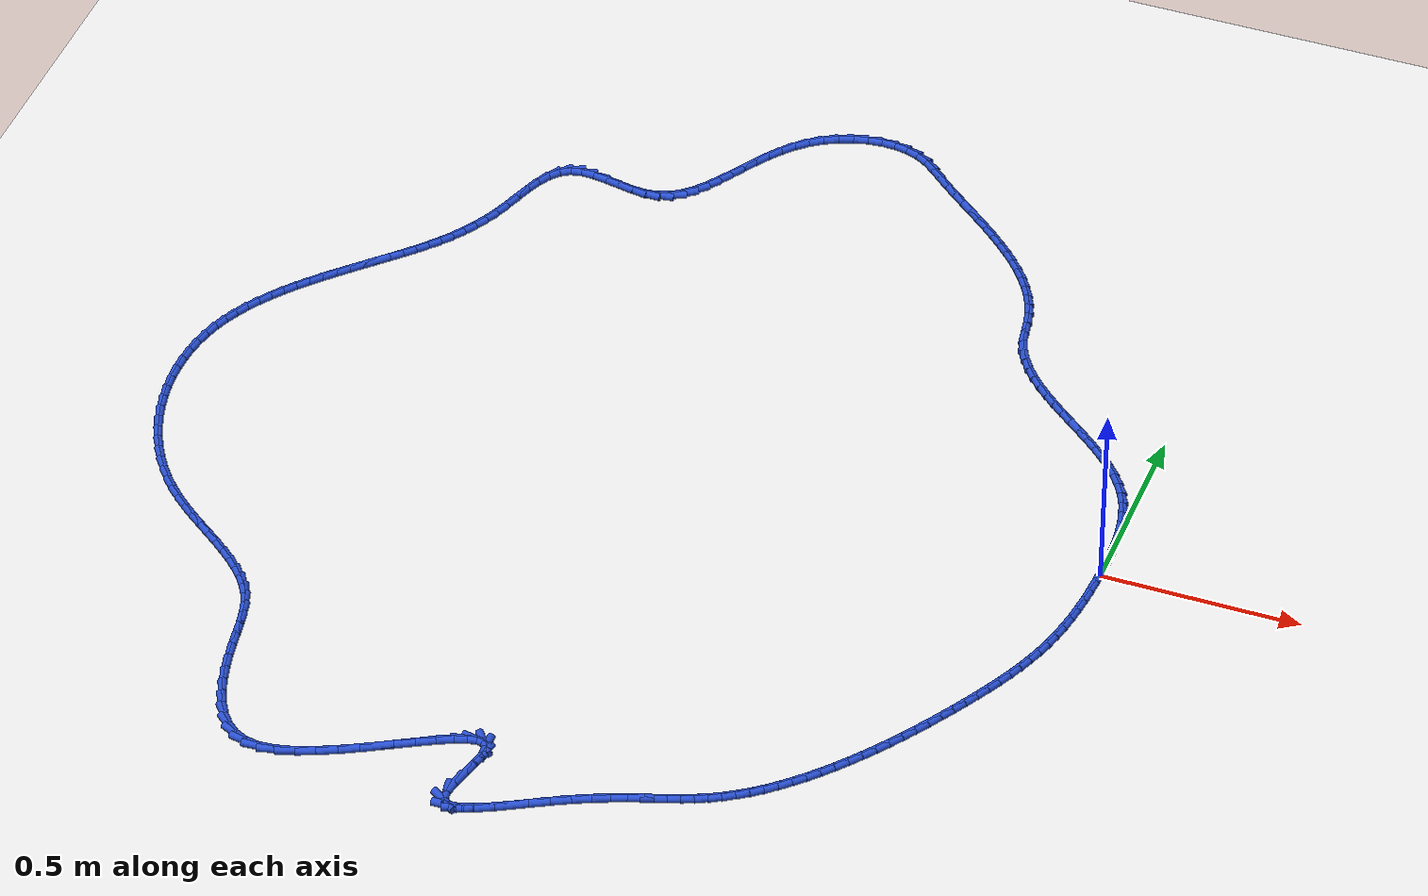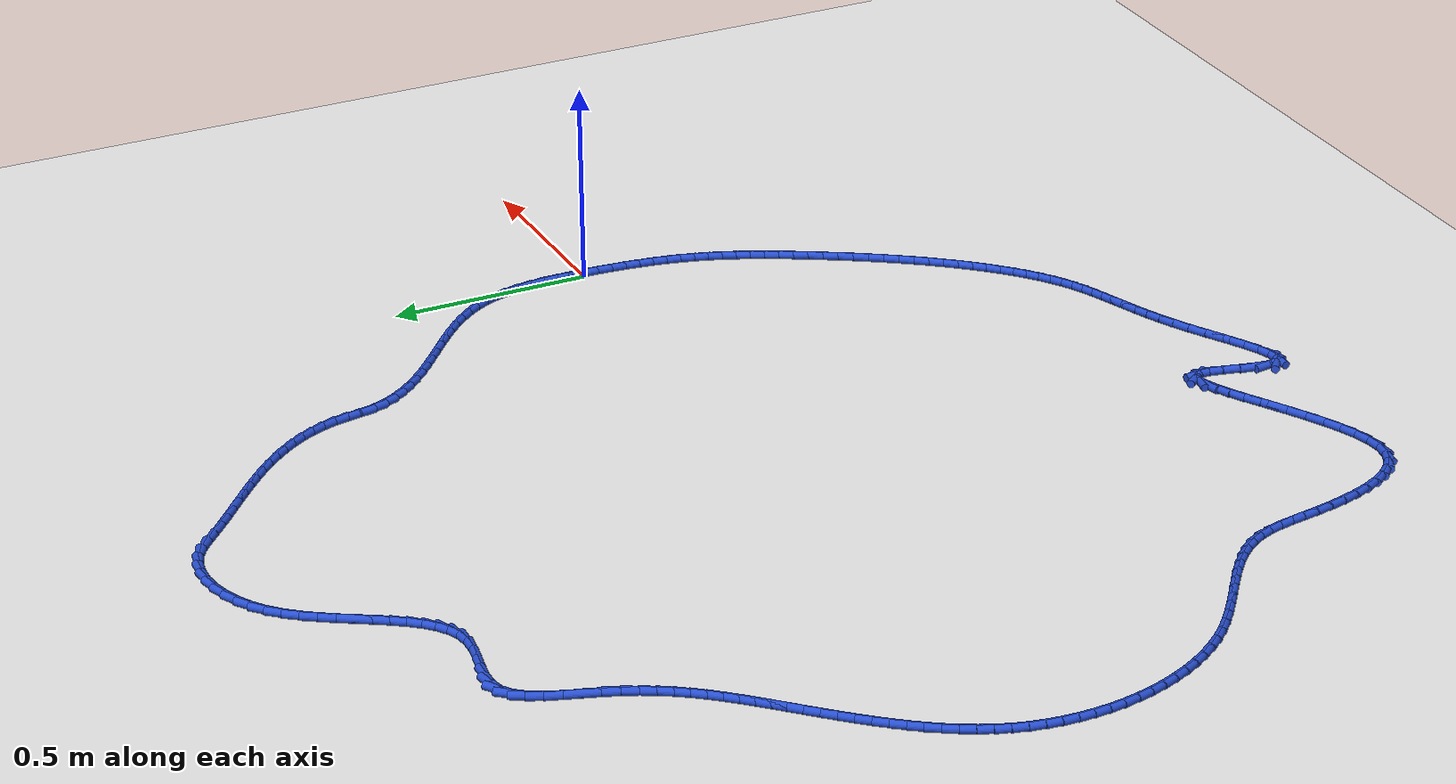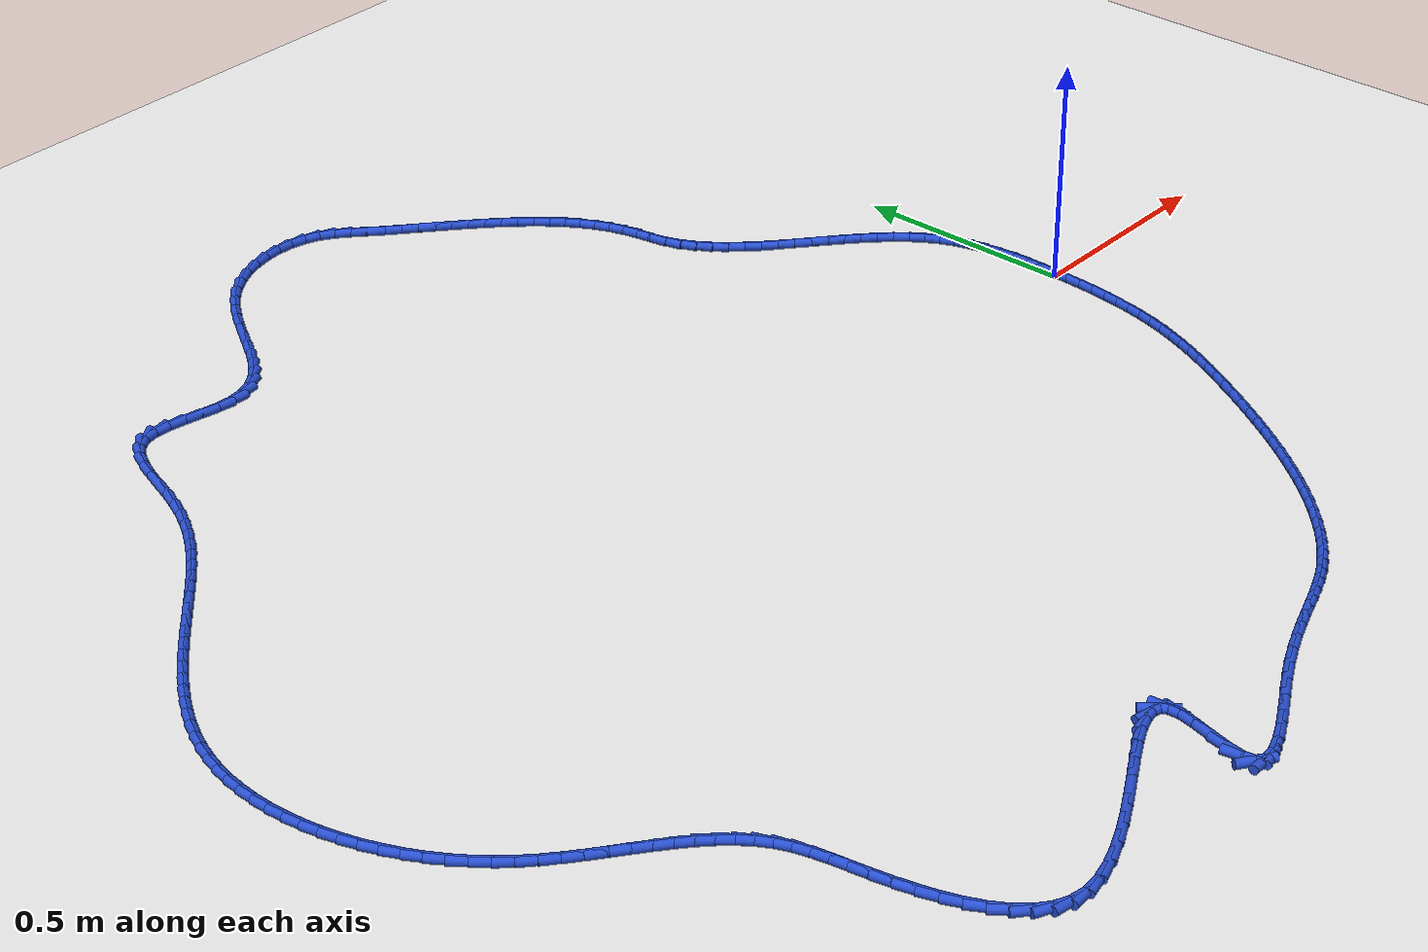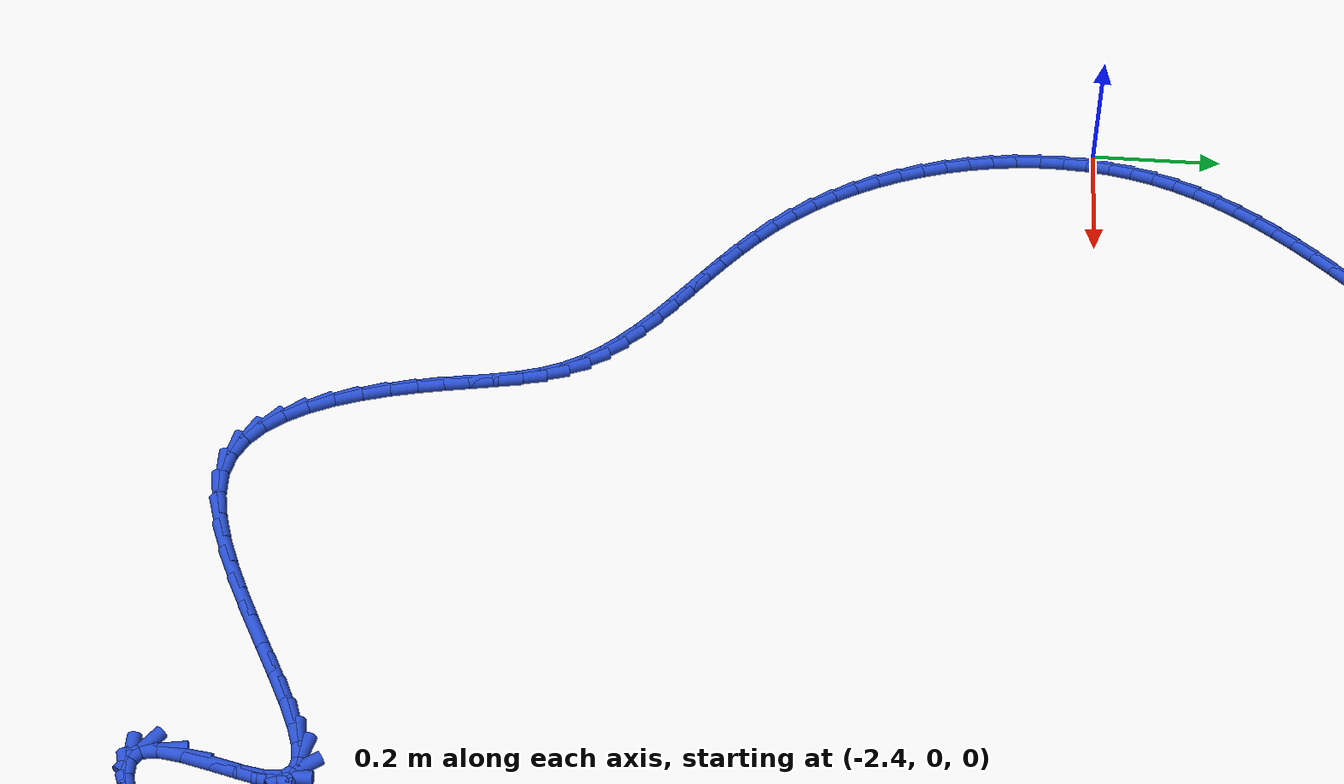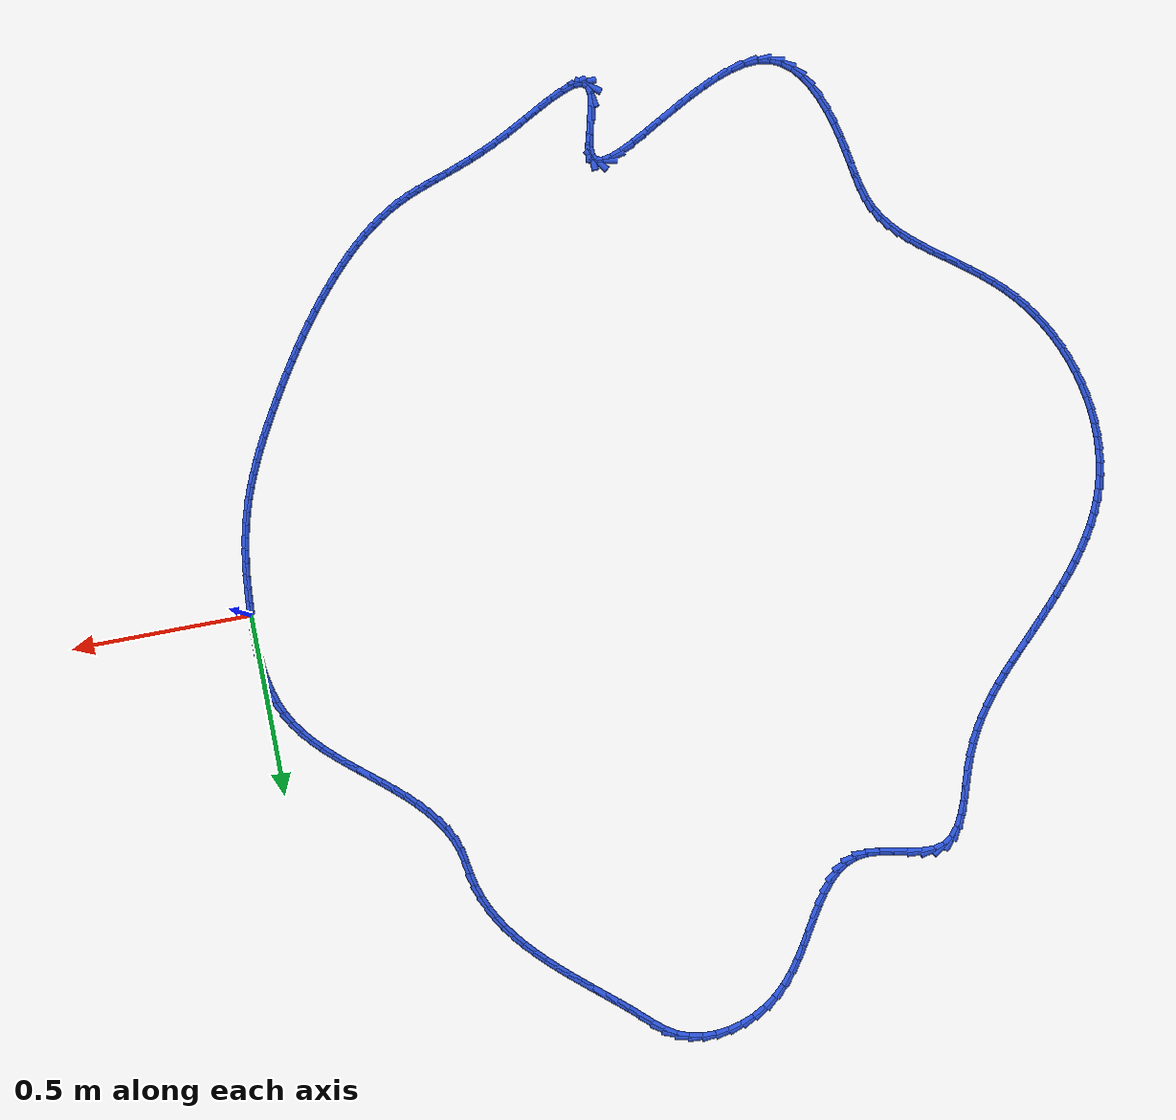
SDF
<sdf version="1.6">
 <world name="default">
  <light name="sun" type="directional">
   <pose>0 0 10 0 -0 0</pose>
   <diffuse>0.8 0.8 0.8 1</diffuse>
   <specular>0.2 0.2 0.2 1</specular>
   <attenuation>
    <range>1000</range>
    <constant>0.9</constant>
    <linear>0.01</linear>
    <quadratic>0.001</quadratic>
   </attenuation>
   <direction>-0.5 0.1 -0.9</direction>
  </light>
  <model name="ground_plane">
   <static>1</static>
   <link name="link">
    <collision name="collision">
     <geometry><plane><normal>0 0 1</normal><size>100 100</size></plane></geometry>
     <surface><friction><ode><mu>100</mu><mu2>50</mu2></ode></friction></surface>
    </collision>
    <visual name="visual">
     <cast_shadows>0</cast_shadows>
     <geometry><plane><normal>0 0 1</normal><size>100 100</size></plane></geometry>
     <material>
      <script><uri>file://media/materials/scripts/gazebo.material</uri><name>Gazebo/WhiteGlow</name></script>
     </material>
    </visual>
   </link>
  </model>
  <gravity>0 0 -9.8</gravity>
  <magnetic_field>6e-06 2.3e-05 -4.2e-05</magnetic_field>
  <atmosphere type="adiabatic"/>
  <physics name="default_physics" default="0" type="ode">
   <max_step_size>0.001</max_step_size>
   <real_time_factor>1</real_time_factor>
   <real_time_update_rate>1000</real_time_update_rate>
  </physics>
  <scene><ambient>0.4 0.4 0.4 1</ambient><background>0.7 0.7 0.7 1</background><shadows>1</shadows></scene>
  <spherical_coordinates>
   <surface_model>EARTH_WGS84</surface_model>
   <latitude_deg>0</latitude_deg>
   <longitude_deg>0</longitude_deg>
   <elevation>0</elevation>
   <heading_deg>0</heading_deg>
  </spherical_coordinates>
  <model name="line">
   <link name="link_0">
    <pose>-1.2576745200831851e-17 3.469446951953614e-17 0.01 0 1.57 1.5442208761935035</pose>
    <collision name="collision">
     <geometry><cylinder><radius>0.01</radius><length>0.08</length></cylinder></geometry>
    </collision>
    <visual name="visual">
     <material>
      <script><name>Gazebo/Blue</name><uri>file://media/materials/scripts/gazebo.material</uri></script>
     </material>
     <geometry><cylinder><radius>0.01</radius><length>0.08</length></cylinder></geometry>
    </visual>
   </link>
   <link name="link_1">
    <pose>0.0009799392544859362 0.03686517164998687 0.01 0 1.57 -1.570191355124968</pose>
    <collision name="collision">
     <geometry><cylinder><radius>0.01</radius><length>0.08</length></cylinder></geometry>
    </collision>
    <visual name="visual">
     <material>
      <script><name>Gazebo/Blue</name><uri>file://media/materials/scripts/gazebo.material</uri></script>
     </material>
     <geometry><cylinder><radius>0.01</radius><length>0.08</length></cylinder></geometry>
    </visual>
   </link>
   <link name="link_2">
    <pose>0.0009576036723028721 0.07378521364273605 0.01 0 1.57 -1.5329855789430364</pose>
    <collision name="collision">
     <geometry><cylinder><radius>0.01</radius><length>0.08</length></cylinder></geometry>
    </collision>
    <visual name="visual">
     <material>
      <script><name>Gazebo/Blue</name><uri>file://media/materials/scripts/gazebo.material</uri></script>
     </material>
     <geometry><cylinder><radius>0.01</radius><length>0.08</length></cylinder></geometry>
    </visual>
   </link>
   <link name="link_3">
    <pose>-0.00043132697029535805 0.11050145868547574 0.01 0 1.57 -1.4849520792522348</pose>
    <collision name="collision">
     <geometry><cylinder><radius>0.01</radius><length>0.08</length></cylinder></geometry>
    </collision>
    <visual name="visual">
     <material>
      <script><name>Gazebo/Blue</name><uri>file://media/materials/scripts/gazebo.material</uri></script>
     </material>
     <geometry><cylinder><radius>0.01</radius><length>0.08</length></cylinder></geometry>
    </visual>
   </link>
   <link name="link_4">
    <pose>-0.0035511728970549113 0.1467552394854341 0.01 0 1.57 -1.4250680438499683</pose>
    <collision name="collision">
     <geometry><cylinder><radius>0.01</radius><length>0.08</length></cylinder></geometry>
    </collision>
    <visual name="visual">
     <material>
      <script><name>Gazebo/Blue</name><uri>file://media/materials/scripts/gazebo.material</uri></script>
     </material>
     <geometry><cylinder><radius>0.01</radius><length>0.08</length></cylinder></geometry>
    </visual>
   </link>
   <link name="link_5">
    <pose>-0.008766254331721943 0.18228788874983937 0.01 0 1.57 -1.352231468510381</pose>
    <collision name="collision">
     <geometry><cylinder><radius>0.01</radius><length>0.08</length></cylinder></geometry>
    </collision>
    <visual name="visual">
     <material>
      <script><name>Gazebo/Blue</name><uri>file://media/materials/scripts/gazebo.material</uri></script>
     </material>
     <geometry><cylinder><radius>0.01</radius><length>0.08</length></cylinder></geometry>
    </visual>
   </link>
   <link name="link_6">
    <pose>-0.016440891498042606 0.21684073918591967 0.01 0 1.57 -1.2655131130697617</pose>
    <collision name="collision">
     <geometry><cylinder><radius>0.01</radius><length>0.08</length></cylinder></geometry>
    </collision>
    <visual name="visual">
     <material>
      <script><name>Gazebo/Blue</name><uri>file://media/materials/scripts/gazebo.material</uri></script>
     </material>
     <geometry><cylinder><radius>0.01</radius><length>0.08</length></cylinder></geometry>
    </visual>
   </link>
   <link name="link_7">
    <pose>-0.026939404619763057 0.2501551235009031 0.01 0 1.57 -1.1645579242230624</pose>
    <collision name="collision">
     <geometry><cylinder><radius>0.01</radius><length>0.08</length></cylinder></geometry>
    </collision>
    <visual name="visual">
     <material>
      <script><name>Gazebo/Blue</name><uri>file://media/materials/scripts/gazebo.material</uri></script>
     </material>
     <geometry><cylinder><radius>0.01</radius><length>0.08</length></cylinder></geometry>
    </visual>
   </link>
   <link name="link_8">
    <pose>-0.040626113857494914 0.28197237443907197 0.01 0 1.57 -1.054779717884498</pose>
    <collision name="collision">
     <geometry><cylinder><radius>0.01</radius><length>0.08</length></cylinder></geometry>
    </collision>
    <visual name="visual">
     <material>
      <script><name>Gazebo/Blue</name><uri>file://media/materials/scripts/gazebo.material</uri></script>
     </material>
     <geometry><cylinder><radius>0.01</radius><length>0.08</length></cylinder></geometry>
    </visual>
   </link>
   <link name="link_9">
    <pose>-0.05772592724237543 0.3121156462107354 0.01 0 1.57 -0.9562241087145369</pose>
    <collision name="collision">
     <geometry><cylinder><radius>0.01</radius><length>0.08</length></cylinder></geometry>
    </collision>
    <visual name="visual">
     <material>
      <script><name>Gazebo/Blue</name><uri>file://media/materials/scripts/gazebo.material</uri></script>
     </material>
     <geometry><cylinder><radius>0.01</radius><length>0.08</length></cylinder></geometry>
    </visual>
   </link>
   <link name="link_10">
    <pose>-0.07791890071605993 0.3407278686217521 0.01 0 1.57 -0.87430412471775</pose>
    <collision name="collision">
     <geometry><cylinder><radius>0.01</radius><length>0.08</length></cylinder></geometry>
    </collision>
    <visual name="visual">
     <material>
      <script><name>Gazebo/Blue</name><uri>file://media/materials/scripts/gazebo.material</uri></script>
     </material>
     <geometry><cylinder><radius>0.01</radius><length>0.08</length></cylinder></geometry>
    </visual>
   </link>
   <link name="link_11">
    <pose>-0.10075200322788812 0.3680300806989035 0.01 0 1.57 -0.8086803140303752</pose>
    <collision name="collision">
     <geometry><cylinder><radius>0.01</radius><length>0.08</length></cylinder></geometry>
    </collision>
    <visual name="visual">
     <material>
      <script><name>Gazebo/Blue</name><uri>file://media/materials/scripts/gazebo.material</uri></script>
     </material>
     <geometry><cylinder><radius>0.01</radius><length>0.08</length></cylinder></geometry>
    </visual>
   </link>
   <link name="link_12">
    <pose>-0.12577220372719977 0.39424332146897073 0.01 0 1.57 -0.758361175305445</pose>
    <collision name="collision">
     <geometry><cylinder><radius>0.01</radius><length>0.08</length></cylinder></geometry>
    </collision>
    <visual name="visual">
     <material>
      <script><name>Gazebo/Blue</name><uri>file://media/materials/scripts/gazebo.material</uri></script>
     </material>
     <geometry><cylinder><radius>0.01</radius><length>0.08</length></cylinder></geometry>
    </visual>
   </link>
   <link name="link_13">
    <pose>-0.1525264711633347 0.41958862995873547 0.01 0 1.57 -0.7222043457416181</pose>
    <collision name="collision">
     <geometry><cylinder><radius>0.01</radius><length>0.08</length></cylinder></geometry>
    </collision>
    <visual name="visual">
     <material>
      <script><name>Gazebo/Blue</name><uri>file://media/materials/scripts/gazebo.material</uri></script>
     </material>
     <geometry><cylinder><radius>0.01</radius><length>0.08</length></cylinder></geometry>
    </visual>
   </link>
   <link name="link_14">
    <pose>-0.18056177448563257 0.444287045194979 0.01 0 1.57 -0.6992157820411935</pose>
    <collision name="collision">
     <geometry><cylinder><radius>0.01</radius><length>0.08</length></cylinder></geometry>
    </collision>
    <visual name="visual">
     <material>
      <script><name>Gazebo/Blue</name><uri>file://media/materials/scripts/gazebo.material</uri></script>
     </material>
     <geometry><cylinder><radius>0.01</radius><length>0.08</length></cylinder></geometry>
    </visual>
   </link>
   <link name="link_15">
    <pose>-0.20942508264343312 0.46855960620448256 0.01 0 1.57 -0.6887034426502311</pose>
    <collision name="collision">
     <geometry><cylinder><radius>0.01</radius><length>0.08</length></cylinder></geometry>
    </collision>
    <visual name="visual">
     <material>
      <script><name>Gazebo/Blue</name><uri>file://media/materials/scripts/gazebo.material</uri></script>
     </material>
     <geometry><cylinder><radius>0.01</radius><length>0.08</length></cylinder></geometry>
    </visual>
   </link>
   <link name="link_16">
    <pose>-0.2386633645860762 0.49262735201402774 0.01 0 1.57 -0.6903463337132321</pose>
    <collision name="collision">
     <geometry><cylinder><radius>0.01</radius><length>0.08</length></cylinder></geometry>
    </collision>
    <visual name="visual">
     <material>
      <script><name>Gazebo/Blue</name><uri>file://media/materials/scripts/gazebo.material</uri></script>
     </material>
     <geometry><cylinder><radius>0.01</radius><length>0.08</length></cylinder></geometry>
    </visual>
   </link>
   <link name="link_17">
    <pose>-0.2678235892629014 0.5167113216503956 0.01 0 1.57 -0.7042195649220782</pose>
    <collision name="collision">
     <geometry><cylinder><radius>0.01</radius><length>0.08</length></cylinder></geometry>
    </collision>
    <visual name="visual">
     <material>
      <script><name>Gazebo/Blue</name><uri>file://media/materials/scripts/gazebo.material</uri></script>
     </material>
     <geometry><cylinder><radius>0.01</radius><length>0.08</length></cylinder></geometry>
    </visual>
   </link>
   <link name="link_18">
    <pose>-0.29645272562324876 0.5410325541403679 0.01 0 1.57 -0.7307933267280785</pose>
    <collision name="collision">
     <geometry><cylinder><radius>0.01</radius><length>0.08</length></cylinder></geometry>
    </collision>
    <visual name="visual">
     <material>
      <script><name>Gazebo/Blue</name><uri>file://media/materials/scripts/gazebo.material</uri></script>
     </material>
     <geometry><cylinder><radius>0.01</radius><length>0.08</length></cylinder></geometry>
    </visual>
   </link>
   <link name="link_19">
    <pose>-0.32409774261645763 0.5658120885107256 0.01 0 1.57 -0.770902594090019</pose>
    <collision name="collision">
     <geometry><cylinder><radius>0.01</radius><length>0.08</length></cylinder></geometry>
    </collision>
    <visual name="visual">
     <material>
      <script><name>Gazebo/Blue</name><uri>file://media/materials/scripts/gazebo.material</uri></script>
     </material>
     <geometry><cylinder><radius>0.01</radius><length>0.08</length></cylinder></geometry>
    </visual>
   </link>
   <link name="link_20">
    <pose>-0.35030560919186793 0.5912709637882504 0.01 0 1.57 -0.8256623684526592</pose>
    <collision name="collision">
     <geometry><cylinder><radius>0.01</radius><length>0.08</length></cylinder></geometry>
    </collision>
    <visual name="visual">
     <material>
      <script><name>Gazebo/Blue</name><uri>file://media/materials/scripts/gazebo.material</uri></script>
     </material>
     <geometry><cylinder><radius>0.01</radius><length>0.08</length></cylinder></geometry>
    </visual>
   </link>
   <link name="link_21">
    <pose>-0.37462329429881946 0.6176302189997235 0.01 0 1.57 -0.8962787909941068</pose>
    <collision name="collision">
     <geometry><cylinder><radius>0.01</radius><length>0.08</length></cylinder></geometry>
    </collision>
    <visual name="visual">
     <material>
      <script><name>Gazebo/Blue</name><uri>file://media/materials/scripts/gazebo.material</uri></script>
     </material>
     <geometry><cylinder><radius>0.01</radius><length>0.08</length></cylinder></geometry>
    </visual>
   </link>
   <link name="link_22">
    <pose>-0.39659776688665194 0.6451108931719263 0.01 0 1.57 -0.98368758642964</pose>
    <collision name="collision">
     <geometry><cylinder><radius>0.01</radius><length>0.08</length></cylinder></geometry>
    </collision>
    <visual name="visual">
     <material>
      <script><name>Gazebo/Blue</name><uri>file://media/materials/scripts/gazebo.material</uri></script>
     </material>
     <geometry><cylinder><radius>0.01</radius><length>0.08</length></cylinder></geometry>
    </visual>
   </link>
   <link name="link_23">
    <pose>-0.41577599590470515 0.6739340253316402 0.01 0 1.57 -1.0879693595745252</pose>
    <collision name="collision">
     <geometry><cylinder><radius>0.01</radius><length>0.08</length></cylinder></geometry>
    </collision>
    <visual name="visual">
     <material>
      <script><name>Gazebo/Blue</name><uri>file://media/materials/scripts/gazebo.material</uri></script>
     </material>
     <geometry><cylinder><radius>0.01</radius><length>0.08</length></cylinder></geometry>
    </visual>
   </link>
   <link name="link_24">
    <pose>-0.4317049503023187 0.7043206545056464 0.01 0 1.57 -1.2076056975408678</pose>
    <collision name="collision">
     <geometry><cylinder><radius>0.01</radius><length>0.08</length></cylinder></geometry>
    </collision>
    <visual name="visual">
     <material>
      <script><name>Gazebo/Blue</name><uri>file://media/materials/scripts/gazebo.material</uri></script>
     </material>
     <geometry><cylinder><radius>0.01</radius><length>0.08</length></cylinder></geometry>
    </visual>
   </link>
   <link name="link_25">
    <pose>-0.4439315990288326 0.7364918197207269 0.01 0 1.57 -1.3362297150377422</pose>
    <collision name="collision">
     <geometry><cylinder><radius>0.01</radius><length>0.08</length></cylinder></geometry>
    </collision>
    <visual name="visual">
     <material>
      <script><name>Gazebo/Blue</name><uri>file://media/materials/scripts/gazebo.material</uri></script>
     </material>
     <geometry><cylinder><radius>0.01</radius><length>0.08</length></cylinder></geometry>
    </visual>
   </link>
   <link name="link_26">
    <pose>-0.452088937798595 0.7706278690755644 0.01 0 1.57 -1.4055876978040331</pose>
    <collision name="collision">
     <geometry><cylinder><radius>0.01</radius><length>0.08</length></cylinder></geometry>
    </collision>
    <visual name="visual">
     <material>
      <script><name>Gazebo/Blue</name><uri>file://media/materials/scripts/gazebo.material</uri></script>
     </material>
     <geometry><cylinder><radius>0.01</radius><length>0.08</length></cylinder></geometry>
    </visual>
   </link>
   <link name="link_27">
    <pose>-0.45796787422412355 0.8058884516122022 0.01 0 1.57 -1.3576633662700424</pose>
    <collision name="collision">
     <geometry><cylinder><radius>0.01</radius><length>0.08</length></cylinder></geometry>
    </collision>
    <visual name="visual">
     <material>
      <script><name>Gazebo/Blue</name><uri>file://media/materials/scripts/gazebo.material</uri></script>
     </material>
     <geometry><cylinder><radius>0.01</radius><length>0.08</length></cylinder></geometry>
    </visual>
   </link>
   <link name="link_28">
    <pose>-0.4654466397236207 0.8404451829258839 0.01 0 1.57 -1.2599925563201273</pose>
    <collision name="collision">
     <geometry><cylinder><radius>0.01</radius><length>0.08</length></cylinder></geometry>
    </collision>
    <visual name="visual">
     <material>
      <script><name>Gazebo/Blue</name><uri>file://media/materials/scripts/gazebo.material</uri></script>
     </material>
     <geometry><cylinder><radius>0.01</radius><length>0.08</length></cylinder></geometry>
    </visual>
   </link>
   <link name="link_29">
    <pose>-0.4760827379401297 0.8735573726928375 0.01 0 1.57 -1.1668296043280926</pose>
    <collision name="collision">
     <geometry><cylinder><radius>0.01</radius><length>0.08</length></cylinder></geometry>
    </collision>
    <visual name="visual">
     <material>
      <script><name>Gazebo/Blue</name><uri>file://media/materials/scripts/gazebo.material</uri></script>
     </material>
     <geometry><cylinder><radius>0.01</radius><length>0.08</length></cylinder></geometry>
    </visual>
   </link>
   <link name="link_30">
    <pose>-0.4896590019854619 0.9053164324322291 0.01 0 1.57 -1.0812638315535197</pose>
    <collision name="collision">
     <geometry><cylinder><radius>0.01</radius><length>0.08</length></cylinder></geometry>
    </collision>
    <visual name="visual">
     <material>
      <script><name>Gazebo/Blue</name><uri>file://media/materials/scripts/gazebo.material</uri></script>
     </material>
     <geometry><cylinder><radius>0.01</radius><length>0.08</length></cylinder></geometry>
    </visual>
   </link>
   <link name="link_31">
    <pose>-0.5059177371899706 0.9358327761997773 0.01 0 1.57 -1.0044408117792067</pose>
    <collision name="collision">
     <geometry><cylinder><radius>0.01</radius><length>0.08</length></cylinder></geometry>
    </collision>
    <visual name="visual">
     <material>
      <script><name>Gazebo/Blue</name><uri>file://media/materials/scripts/gazebo.material</uri></script>
     </material>
     <geometry><cylinder><radius>0.01</radius><length>0.08</length></cylinder></geometry>
    </visual>
   </link>
   <link name="link_32">
    <pose>-0.5246012488840094 0.9652168180512024 0.01 0 1.57 -0.9368635857762895</pose>
    <collision name="collision">
     <geometry><cylinder><radius>0.01</radius><length>0.08</length></cylinder></geometry>
    </collision>
    <visual name="visual">
     <material>
      <script><name>Gazebo/Blue</name><uri>file://media/materials/scripts/gazebo.material</uri></script>
     </material>
     <geometry><cylinder><radius>0.01</radius><length>0.08</length></cylinder></geometry>
    </visual>
   </link>
   <link name="link_33">
    <pose>-0.5454518423979314 0.9935789720422238 0.01 0 1.57 -0.8785481963484082</pose>
    <collision name="collision">
     <geometry><cylinder><radius>0.01</radius><length>0.08</length></cylinder></geometry>
    </collision>
    <visual name="visual">
     <material>
      <script><name>Gazebo/Blue</name><uri>file://media/materials/scripts/gazebo.material</uri></script>
     </material>
     <geometry><cylinder><radius>0.01</radius><length>0.08</length></cylinder></geometry>
    </visual>
   </link>
   <link name="link_34">
    <pose>-0.5682118230620903 1.02102965222856 0.01 0 1.57 -0.8291987761525833</pose>
    <collision name="collision">
     <geometry><cylinder><radius>0.01</radius><length>0.08</length></cylinder></geometry>
    </collision>
    <visual name="visual">
     <material>
      <script><name>Gazebo/Blue</name><uri>file://media/materials/scripts/gazebo.material</uri></script>
     </material>
     <geometry><cylinder><radius>0.01</radius><length>0.08</length></cylinder></geometry>
    </visual>
   </link>
   <link name="link_35">
    <pose>-0.5926234962068395 1.0476792726659319 0.01 0 1.57 -0.7883597086406142</pose>
    <collision name="collision">
     <geometry><cylinder><radius>0.01</radius><length>0.08</length></cylinder></geometry>
    </collision>
    <visual name="visual">
     <material>
      <script><name>Gazebo/Blue</name><uri>file://media/materials/scripts/gazebo.material</uri></script>
     </material>
     <geometry><cylinder><radius>0.01</radius><length>0.08</length></cylinder></geometry>
    </visual>
   </link>
   <link name="link_36">
    <pose>-0.6184291671625328 1.0736382474100583 0.01 0 1.57 -0.7555291905596424</pose>
    <collision name="collision">
     <geometry><cylinder><radius>0.01</radius><length>0.08</length></cylinder></geometry>
    </collision>
    <visual name="visual">
     <material>
      <script><name>Gazebo/Blue</name><uri>file://media/materials/scripts/gazebo.material</uri></script>
     </material>
     <geometry><cylinder><radius>0.01</radius><length>0.08</length></cylinder></geometry>
    </visual>
   </link>
   <link name="link_37">
    <pose>-0.6453711412595232 1.0990169905166594 0.01 0 1.57 -0.7302354427312308</pose>
    <collision name="collision">
     <geometry><cylinder><radius>0.01</radius><length>0.08</length></cylinder></geometry>
    </collision>
    <visual name="visual">
     <material>
      <script><name>Gazebo/Blue</name><uri>file://media/materials/scripts/gazebo.material</uri></script>
     </material>
     <geometry><cylinder><radius>0.01</radius><length>0.08</length></cylinder></geometry>
    </visual>
   </link>
   <link name="link_38">
    <pose>-0.6731917238281643 1.1239259160414536 0.01 0 1.57 -0.7120838756087301</pose>
    <collision name="collision">
     <geometry><cylinder><radius>0.01</radius><length>0.08</length></cylinder></geometry>
    </collision>
    <visual name="visual">
     <material>
      <script><name>Gazebo/Blue</name><uri>file://media/materials/scripts/gazebo.material</uri></script>
     </material>
     <geometry><cylinder><radius>0.01</radius><length>0.08</length></cylinder></geometry>
    </visual>
   </link>
   <link name="link_39">
    <pose>-0.7016332201988096 1.1484754380401612 0.01 0 1.57 -0.7007845174598353</pose>
    <collision name="collision">
     <geometry><cylinder><radius>0.01</radius><length>0.08</length></cylinder></geometry>
    </collision>
    <visual name="visual">
     <material>
      <script><name>Gazebo/Blue</name><uri>file://media/materials/scripts/gazebo.material</uri></script>
     </material>
     <geometry><cylinder><radius>0.01</radius><length>0.08</length></cylinder></geometry>
    </visual>
   </link>
   <link name="link_40">
    <pose>-0.7304379357018123 1.1727759705685012 0.01 0 1.57 -0.6961673746985062</pose>
    <collision name="collision">
     <geometry><cylinder><radius>0.01</radius><length>0.08</length></cylinder></geometry>
    </collision>
    <visual name="visual">
     <material>
      <script><name>Gazebo/Blue</name><uri>file://media/materials/scripts/gazebo.material</uri></script>
     </material>
     <geometry><cylinder><radius>0.01</radius><length>0.08</length></cylinder></geometry>
    </visual>
   </link>
   <link name="link_41">
    <pose>-0.759348175667526 1.1969379276821934 0.01 0 1.57 -0.6981910785221916</pose>
    <collision name="collision">
     <geometry><cylinder><radius>0.01</radius><length>0.08</length></cylinder></geometry>
    </collision>
    <visual name="visual">
     <material>
      <script><name>Gazebo/Blue</name><uri>file://media/materials/scripts/gazebo.material</uri></script>
     </material>
     <geometry><cylinder><radius>0.01</radius><length>0.08</length></cylinder></geometry>
    </visual>
   </link>
   <link name="link_42">
    <pose>-0.7881062454263043 1.2210717234369575 0.01 0 1.57 -0.7069479684033514</pose>
    <collision name="collision">
     <geometry><cylinder><radius>0.01</radius><length>0.08</length></cylinder></geometry>
    </collision>
    <visual name="visual">
     <material>
      <script><name>Gazebo/Blue</name><uri>file://media/materials/scripts/gazebo.material</uri></script>
     </material>
     <geometry><cylinder><radius>0.01</radius><length>0.08</length></cylinder></geometry>
    </visual>
   </link>
   <link name="link_43">
    <pose>-0.8164544503085005 1.2452877718885127 0.01 0 1.57 -0.7226667909168422</pose>
    <collision name="collision">
     <geometry><cylinder><radius>0.01</radius><length>0.08</length></cylinder></geometry>
    </collision>
    <visual name="visual">
     <material>
      <script><name>Gazebo/Blue</name><uri>file://media/materials/scripts/gazebo.material</uri></script>
     </material>
     <geometry><cylinder><radius>0.01</radius><length>0.08</length></cylinder></geometry>
    </visual>
   </link>
   <link name="link_44">
    <pose>-0.844135095644468 1.2696964870925784 0.01 0 1.57 -0.737305310171386</pose>
    <collision name="collision">
     <geometry><cylinder><radius>0.01</radius><length>0.08</length></cylinder></geometry>
    </collision>
    <visual name="visual">
     <material>
      <script><name>Gazebo/Blue</name><uri>file://media/materials/scripts/gazebo.material</uri></script>
     </material>
     <geometry><cylinder><radius>0.01</radius><length>0.08</length></cylinder></geometry>
    </visual>
   </link>
   <link name="link_45">
    <pose>-0.8710774708853611 1.2941644829262386 0.01 0 1.57 -0.6911209274750407</pose>
    <collision name="collision">
     <geometry><cylinder><radius>0.01</radius><length>0.08</length></cylinder></geometry>
    </collision>
    <visual name="visual">
     <material>
      <script><name>Gazebo/Blue</name><uri>file://media/materials/scripts/gazebo.material</uri></script>
     </material>
     <geometry><cylinder><radius>0.01</radius><length>0.08</length></cylinder></geometry>
    </visual>
   </link>
   <link name="link_46">
    <pose>-0.8985133816809016 1.3168600810237472 0.01 0 1.57 -0.554242211140613</pose>
    <collision name="collision">
     <geometry><cylinder><radius>0.01</radius><length>0.08</length></cylinder></geometry>
    </collision>
    <visual name="visual">
     <material>
      <script><name>Gazebo/Blue</name><uri>file://media/materials/scripts/gazebo.material</uri></script>
     </material>
     <geometry><cylinder><radius>0.01</radius><length>0.08</length></cylinder></geometry>
    </visual>
   </link>
   <link name="link_47">
    <pose>-0.9282148182977124 1.3352440026054444 0.01 0 1.57 -0.36505649039442806</pose>
    <collision name="collision">
     <geometry><cylinder><radius>0.01</radius><length>0.08</length></cylinder></geometry>
    </collision>
    <visual name="visual">
     <material>
      <script><name>Gazebo/Blue</name><uri>file://media/materials/scripts/gazebo.material</uri></script>
     </material>
     <geometry><cylinder><radius>0.01</radius><length>0.08</length></cylinder></geometry>
    </visual>
   </link>
   <link name="link_48">
    <pose>-0.9610147359703501 1.3477796981426244 0.01 0 1.57 -0.19018767333489905</pose>
    <collision name="collision">
     <geometry><cylinder><radius>0.01</radius><length>0.08</length></cylinder></geometry>
    </collision>
    <visual name="visual">
     <material>
      <script><name>Gazebo/Blue</name><uri>file://media/materials/scripts/gazebo.material</uri></script>
     </material>
     <geometry><cylinder><radius>0.01</radius><length>0.08</length></cylinder></geometry>
    </visual>
   </link>
   <link name="link_49">
    <pose>-0.9962229987667067 1.354557797820425 0.01 0 1.57 -0.0342229439930538</pose>
    <collision name="collision">
     <geometry><cylinder><radius>0.01</radius><length>0.08</length></cylinder></geometry>
    </collision>
    <visual name="visual">
     <material>
      <script><name>Gazebo/Blue</name><uri>file://media/materials/scripts/gazebo.material</uri></script>
     </material>
     <geometry><cylinder><radius>0.01</radius><length>0.08</length></cylinder></geometry>
    </visual>
   </link>
   <link name="link_50">
    <pose>-1.0330106212900723 1.3558172703062894 0.01 0 1.57 0.10668978763686991</pose>
    <collision name="collision">
     <geometry><cylinder><radius>0.01</radius><length>0.08</length></cylinder></geometry>
    </collision>
    <visual name="visual">
     <material>
      <script><name>Gazebo/Blue</name><uri>file://media/materials/scripts/gazebo.material</uri></script>
     </material>
     <geometry><cylinder><radius>0.01</radius><length>0.08</length></cylinder></geometry>
    </visual>
   </link>
   <link name="link_51">
    <pose>-1.0705486181437374 1.3517970842676603 0.01 0 1.57 0.23732686594858204</pose>
    <collision name="collision">
     <geometry><cylinder><radius>0.01</radius><length>0.08</length></cylinder></geometry>
    </collision>
    <visual name="visual">
     <material>
      <script><name>Gazebo/Blue</name><uri>file://media/materials/scripts/gazebo.material</uri></script>
     </material>
     <geometry><cylinder><radius>0.01</radius><length>0.08</length></cylinder></geometry>
    </visual>
   </link>
   <link name="link_52">
    <pose>-1.1080080039309923 1.3427362083719816 0.01 0 1.57 0.3624993980727459</pose>
    <collision name="collision">
     <geometry><cylinder><radius>0.01</radius><length>0.08</length></cylinder></geometry>
    </collision>
    <visual name="visual">
     <material>
      <script><name>Gazebo/Blue</name><uri>file://media/materials/scripts/gazebo.material</uri></script>
     </material>
     <geometry><cylinder><radius>0.01</radius><length>0.08</length></cylinder></geometry>
    </visual>
   </link>
   <link name="link_53">
    <pose>-1.1445597932551268 1.3288736112866963 0.01 0 1.57 0.48675943279520245</pose>
    <collision name="collision">
     <geometry><cylinder><radius>0.01</radius><length>0.08</length></cylinder></geometry>
    </collision>
    <visual name="visual">
     <material>
      <script><name>Gazebo/Blue</name><uri>file://media/materials/scripts/gazebo.material</uri></script>
     </material>
     <geometry><cylinder><radius>0.01</radius><length>0.08</length></cylinder></geometry>
    </visual>
   </link>
   <link name="link_54">
    <pose>-1.1793750007194317 1.3104482616792474 0.01 0 1.57 0.6143458513261607</pose>
    <collision name="collision">
     <geometry><cylinder><radius>0.01</radius><length>0.08</length></cylinder></geometry>
    </collision>
    <visual name="visual">
     <material>
      <script><name>Gazebo/Blue</name><uri>file://media/materials/scripts/gazebo.material</uri></script>
     </material>
     <geometry><cylinder><radius>0.01</radius><length>0.08</length></cylinder></geometry>
    </visual>
   </link>
   <link name="link_55">
    <pose>-1.211624640927197 1.2876991282170782 0.01 0 1.57 0.7431959846560838</pose>
    <collision name="collision">
     <geometry><cylinder><radius>0.01</radius><length>0.08</length></cylinder></geometry>
    </collision>
    <visual name="visual">
     <material>
      <script><name>Gazebo/Blue</name><uri>file://media/materials/scripts/gazebo.material</uri></script>
     </material>
     <geometry><cylinder><radius>0.01</radius><length>0.08</length></cylinder></geometry>
    </visual>
   </link>
   <link name="link_56">
    <pose>-1.2407058350665834 1.260974462142331 0.01 0 1.57 0.8505720708952734</pose>
    <collision name="collision">
     <geometry><cylinder><radius>0.01</radius><length>0.08</length></cylinder></geometry>
    </collision>
    <visual name="visual">
     <material>
      <script><name>Gazebo/Blue</name><uri>file://media/materials/scripts/gazebo.material</uri></script>
     </material>
     <geometry><cylinder><radius>0.01</radius><length>0.08</length></cylinder></geometry>
    </visual>
   </link>
   <link name="link_57">
    <pose>-1.266944638592874 1.2310714902477464 0.01 0 1.57 0.9305975996019696</pose>
    <collision name="collision">
     <geometry><cylinder><radius>0.01</radius><length>0.08</length></cylinder></geometry>
    </collision>
    <visual name="visual">
     <material>
      <script><name>Gazebo/Blue</name><uri>file://media/materials/scripts/gazebo.material</uri></script>
     </material>
     <geometry><cylinder><radius>0.01</radius><length>0.08</length></cylinder></geometry>
    </visual>
   </link>
   <link name="link_58">
    <pose>-1.2909056326277843 1.1989027243319164 0.01 0 1.57 0.9848673115763239</pose>
    <collision name="collision">
     <geometry><cylinder><radius>0.01</radius><length>0.08</length></cylinder></geometry>
    </collision>
    <visual name="visual">
     <material>
      <script><name>Gazebo/Blue</name><uri>file://media/materials/scripts/gazebo.material</uri></script>
     </material>
     <geometry><cylinder><radius>0.01</radius><length>0.08</length></cylinder></geometry>
    </visual>
   </link>
   <link name="link_59">
    <pose>-1.313153398457429 1.165380676272889 0.01 0 1.57 1.0149041770785605</pose>
    <collision name="collision">
     <geometry><cylinder><radius>0.01</radius><length>0.08</length></cylinder></geometry>
    </collision>
    <visual name="visual">
     <material>
      <script><name>Gazebo/Blue</name><uri>file://media/materials/scripts/gazebo.material</uri></script>
     </material>
     <geometry><cylinder><radius>0.01</radius><length>0.08</length></cylinder></geometry>
    </visual>
   </link>
   <link name="link_60">
    <pose>-1.3342525173679227 1.1314178579487144 0.01 0 1.57 1.0211979084830909</pose>
    <collision name="collision">
     <geometry><cylinder><radius>0.01</radius><length>0.08</length></cylinder></geometry>
    </collision>
    <visual name="visual">
     <material>
      <script><name>Gazebo/Blue</name><uri>file://media/materials/scripts/gazebo.material</uri></script>
     </material>
     <geometry><cylinder><radius>0.01</radius><length>0.08</length></cylinder></geometry>
    </visual>
   </link>
   <link name="link_61">
    <pose>-1.3547675706453786 1.0979267812374394 0.01 0 1.57 1.0026506113990354</pose>
    <collision name="collision">
     <geometry><cylinder><radius>0.01</radius><length>0.08</length></cylinder></geometry>
    </collision>
    <visual name="visual">
     <material>
      <script><name>Gazebo/Blue</name><uri>file://media/materials/scripts/gazebo.material</uri></script>
     </material>
     <geometry><cylinder><radius>0.01</radius><length>0.08</length></cylinder></geometry>
    </visual>
   </link>
   <link name="link_62">
    <pose>-1.3752631395759103 1.0658199580171137 0.01 0 1.57 0.9561720631617506</pose>
    <collision name="collision">
     <geometry><cylinder><radius>0.01</radius><length>0.08</length></cylinder></geometry>
    </collision>
    <visual name="visual">
     <material>
      <script><name>Gazebo/Blue</name><uri>file://media/materials/scripts/gazebo.material</uri></script>
     </material>
     <geometry><cylinder><radius>0.01</radius><length>0.08</length></cylinder></geometry>
    </visual>
   </link>
   <link name="link_63">
    <pose>-1.3963038054456336 1.0360099001657859 0.01 0 1.57 0.8764347328031592</pose>
    <collision name="collision">
     <geometry><cylinder><radius>0.01</radius><length>0.08</length></cylinder></geometry>
    </collision>
    <visual name="visual">
     <material>
      <script><name>Gazebo/Blue</name><uri>file://media/materials/scripts/gazebo.material</uri></script>
     </material>
     <geometry><cylinder><radius>0.01</radius><length>0.08</length></cylinder></geometry>
    </visual>
   </link>
   <link name="link_64">
    <pose>-1.418454149540661 1.009409119561505 0.01 0 1.57 0.7563456995996365</pose>
    <collision name="collision">
     <geometry><cylinder><radius>0.01</radius><length>0.08</length></cylinder></geometry>
    </collision>
    <visual name="visual">
     <material>
      <script><name>Gazebo/Blue</name><uri>file://media/materials/scripts/gazebo.material</uri></script>
     </material>
     <geometry><cylinder><radius>0.01</radius><length>0.08</length></cylinder></geometry>
    </visual>
   </link>
   <link name="link_65">
    <pose>-1.4422787531471073 0.9869301280823193 0.01 0 1.57 0.589834783526708</pose>
    <collision name="collision">
     <geometry><cylinder><radius>0.01</radius><length>0.08</length></cylinder></geometry>
    </collision>
    <visual name="visual">
     <material>
      <script><name>Gazebo/Blue</name><uri>file://media/materials/scripts/gazebo.material</uri></script>
     </material>
     <geometry><cylinder><radius>0.01</radius><length>0.08</length></cylinder></geometry>
    </visual>
   </link>
   <link name="link_66">
    <pose>-1.4683421975510869 0.969485437606277 0.01 0 1.57 0.37904612073650895</pose>
    <collision name="collision">
     <geometry><cylinder><radius>0.01</radius><length>0.08</length></cylinder></geometry>
    </collision>
    <visual name="visual">
     <material>
      <script><name>Gazebo/Blue</name><uri>file://media/materials/scripts/gazebo.material</uri></script>
     </material>
     <geometry><cylinder><radius>0.01</radius><length>0.08</length></cylinder></geometry>
    </visual>
   </link>
   <link name="link_67">
    <pose>-1.497209064038713 0.957987560011428 0.01 0 1.57 0.1429892985234766</pose>
    <collision name="collision">
     <geometry><cylinder><radius>0.01</radius><length>0.08</length></cylinder></geometry>
    </collision>
    <visual name="visual">
     <material>
      <script><name>Gazebo/Blue</name><uri>file://media/materials/scripts/gazebo.material</uri></script>
     </material>
     <geometry><cylinder><radius>0.01</radius><length>0.08</length></cylinder></geometry>
    </visual>
   </link>
   <link name="link_68">
    <pose>-1.5294427304183196 0.9533468193709889 0.01 0 1.57 -0.06030472697664801</pose>
    <collision name="collision">
     <geometry><cylinder><radius>0.01</radius><length>0.08</length></cylinder></geometry>
    </collision>
    <visual name="visual">
     <material>
      <script><name>Gazebo/Blue</name><uri>file://media/materials/scripts/gazebo.material</uri></script>
     </material>
     <geometry><cylinder><radius>0.01</radius><length>0.08</length></cylinder></geometry>
    </visual>
   </link>
   <link name="link_69">
    <pose>-1.5650698978936475 0.9554979142112118 0.01 0 1.57 -0.16752774024930872</pose>
    <collision name="collision">
     <geometry><cylinder><radius>0.01</radius><length>0.08</length></cylinder></geometry>
    </collision>
    <visual name="visual">
     <material>
      <script><name>Gazebo/Blue</name><uri>file://media/materials/scripts/gazebo.material</uri></script>
     </material>
     <geometry><cylinder><radius>0.01</radius><length>0.08</length></cylinder></geometry>
    </visual>
   </link>
   <link name="link_70">
    <pose>-1.6027379409287648 0.9618680620291291 0.01 0 1.57 -0.1971836008499583</pose>
    <collision name="collision">
     <geometry><cylinder><radius>0.01</radius><length>0.08</length></cylinder></geometry>
    </collision>
    <visual name="visual">
     <material>
      <script><name>Gazebo/Blue</name><uri>file://media/materials/scripts/gazebo.material</uri></script>
     </material>
     <geometry><cylinder><radius>0.01</radius><length>0.08</length></cylinder></geometry>
    </visual>
   </link>
   <link name="link_71">
    <pose>-1.6408757001819922 0.9694872072490579 0.01 0 1.57 -0.1579253116276249</pose>
    <collision name="collision">
     <geometry><cylinder><radius>0.01</radius><length>0.08</length></cylinder></geometry>
    </collision>
    <visual name="visual">
     <material>
      <script><name>Gazebo/Blue</name><uri>file://media/materials/scripts/gazebo.material</uri></script>
     </material>
     <geometry><cylinder><radius>0.01</radius><length>0.08</length></cylinder></geometry>
    </visual>
   </link>
   <link name="link_72">
    <pose>-1.677912016311653 0.9753852942953162 0.01 0 1.57 -0.03510904975460567</pose>
    <collision name="collision">
     <geometry><cylinder><radius>0.01</radius><length>0.08</length></cylinder></geometry>
    </collision>
    <visual name="visual">
     <material>
      <script><name>Gazebo/Blue</name><uri>file://media/materials/scripts/gazebo.material</uri></script>
     </material>
     <geometry><cylinder><radius>0.01</radius><length>0.08</length></cylinder></geometry>
    </visual>
   </link>
   <link name="link_73">
    <pose>-1.712275729976069 0.9765922675922217 0.01 0 1.57 0.21108877660209982</pose>
    <collision name="collision">
     <geometry><cylinder><radius>0.01</radius><length>0.08</length></cylinder></geometry>
    </collision>
    <visual name="visual">
     <material>
      <script><name>Gazebo/Blue</name><uri>file://media/materials/scripts/gazebo.material</uri></script>
     </material>
     <geometry><cylinder><radius>0.01</radius><length>0.08</length></cylinder></geometry>
    </visual>
   </link>
   <link name="link_74">
    <pose>-1.7423957131861794 0.9701381290230485 0.01 0 1.57 0.577225130400253</pose>
    <collision name="collision">
     <geometry><cylinder><radius>0.01</radius><length>0.08</length></cylinder></geometry>
    </collision>
    <visual name="visual">
     <material>
      <script><name>Gazebo/Blue</name><uri>file://media/materials/scripts/gazebo.material</uri></script>
     </material>
     <geometry><cylinder><radius>0.01</radius><length>0.08</length></cylinder></geometry>
    </visual>
   </link>
   <link name="link_75">
    <pose>-1.7672071092908515 0.9539807080709972 0.01 0 1.57 0.8830605279883726</pose>
    <collision name="collision">
     <geometry><cylinder><radius>0.01</radius><length>0.08</length></cylinder></geometry>
    </collision>
    <visual name="visual">
     <material>
      <script><name>Gazebo/Blue</name><uri>file://media/materials/scripts/gazebo.material</uri></script>
     </material>
     <geometry><cylinder><radius>0.01</radius><length>0.08</length></cylinder></geometry>
    </visual>
   </link>
   <link name="link_76">
    <pose>-1.787435161290752 0.9293584936979432 0.01 0 1.57 1.076694311883906</pose>
    <collision name="collision">
     <geometry><cylinder><radius>0.01</radius><length>0.08</length></cylinder></geometry>
    </collision>
    <visual name="visual">
     <material>
      <script><name>Gazebo/Blue</name><uri>file://media/materials/scripts/gazebo.material</uri></script>
     </material>
     <geometry><cylinder><radius>0.01</radius><length>0.08</length></cylinder></geometry>
    </visual>
   </link>
   <link name="link_77">
    <pose>-1.8042005687842397 0.8982347157673781 0.01 0 1.57 1.1864615299186125</pose>
    <collision name="collision">
     <geometry><cylinder><radius>0.01</radius><length>0.08</length></cylinder></geometry>
    </collision>
    <visual name="visual">
     <material>
      <script><name>Gazebo/Blue</name><uri>file://media/materials/scripts/gazebo.material</uri></script>
     </material>
     <geometry><cylinder><radius>0.01</radius><length>0.08</length></cylinder></geometry>
    </visual>
   </link>
   <link name="link_78">
    <pose>-1.818624031369676 0.8625726041427915 0.01 0 1.57 1.2383402552903626</pose>
    <collision name="collision">
     <geometry><cylinder><radius>0.01</radius><length>0.08</length></cylinder></geometry>
    </collision>
    <visual name="visual">
     <material>
      <script><name>Gazebo/Blue</name><uri>file://media/materials/scripts/gazebo.material</uri></script>
     </material>
     <geometry><cylinder><radius>0.01</radius><length>0.08</length></cylinder></geometry>
    </visual>
   </link>
   <link name="link_79">
    <pose>-1.8318262486454187 0.8243353886876748 0.01 0 1.57 1.24552917293921</pose>
    <collision name="collision">
     <geometry><cylinder><radius>0.01</radius><length>0.08</length></cylinder></geometry>
    </collision>
    <visual name="visual">
     <material>
      <script><name>Gazebo/Blue</name><uri>file://media/materials/scripts/gazebo.material</uri></script>
     </material>
     <geometry><cylinder><radius>0.01</radius><length>0.08</length></cylinder></geometry>
    </visual>
   </link>
   <link name="link_80">
    <pose>-1.8449279202098283 0.7854862992655179 0.01 0 1.57 1.2108417574941361</pose>
    <collision name="collision">
     <geometry><cylinder><radius>0.01</radius><length>0.08</length></cylinder></geometry>
    </collision>
    <visual name="visual">
     <material>
      <script><name>Gazebo/Blue</name><uri>file://media/materials/scripts/gazebo.material</uri></script>
     </material>
     <geometry><cylinder><radius>0.01</radius><length>0.08</length></cylinder></geometry>
    </visual>
   </link>
   <link name="link_81">
    <pose>-1.8590440778123165 0.7479783395264025 0.01 0 1.57 1.1466663933793373</pose>
    <collision name="collision">
     <geometry><cylinder><radius>0.01</radius><length>0.08</length></cylinder></geometry>
    </collision>
    <visual name="visual">
     <material>
      <script><name>Gazebo/Blue</name><uri>file://media/materials/scripts/gazebo.material</uri></script>
     </material>
     <geometry><cylinder><radius>0.01</radius><length>0.08</length></cylinder></geometry>
    </visual>
   </link>
   <link name="link_82">
    <pose>-1.8748505988281268 0.7129721690774159 0.01 0 1.57 1.0809651333365453</pose>
    <collision name="collision">
     <geometry><cylinder><radius>0.01</radius><length>0.08</length></cylinder></geometry>
    </collision>
    <visual name="visual">
     <material>
      <script><name>Gazebo/Blue</name><uri>file://media/materials/scripts/gazebo.material</uri></script>
     </material>
     <geometry><cylinder><radius>0.01</radius><length>0.08</length></cylinder></geometry>
    </visual>
   </link>
   <link name="link_83">
    <pose>-1.8922786066681083 0.6802847255866363 0.01 0 1.57 1.018498839627627</pose>
    <collision name="collision">
     <geometry><cylinder><radius>0.01</radius><length>0.08</length></cylinder></geometry>
    </collision>
    <visual name="visual">
     <material>
      <script><name>Gazebo/Blue</name><uri>file://media/materials/scripts/gazebo.material</uri></script>
     </material>
     <geometry><cylinder><radius>0.01</radius><length>0.08</length></cylinder></geometry>
    </visual>
   </link>
   <link name="link_84">
    <pose>-1.9111870391027797 0.6496027058194673 0.01 0 1.57 0.9611160336171131</pose>
    <collision name="collision">
     <geometry><cylinder><radius>0.01</radius><length>0.08</length></cylinder></geometry>
    </collision>
    <visual name="visual">
     <material>
      <script><name>Gazebo/Blue</name><uri>file://media/materials/scripts/gazebo.material</uri></script>
     </material>
     <geometry><cylinder><radius>0.01</radius><length>0.08</length></cylinder></geometry>
    </visual>
   </link>
   <link name="link_85">
    <pose>-1.9314348339026592 0.6206128065413111 0.01 0 1.57 0.9104122270428204</pose>
    <collision name="collision">
     <geometry><cylinder><radius>0.01</radius><length>0.08</length></cylinder></geometry>
    </collision>
    <visual name="visual">
     <material>
      <script><name>Gazebo/Blue</name><uri>file://media/materials/scripts/gazebo.material</uri></script>
     </material>
     <geometry><cylinder><radius>0.01</radius><length>0.08</length></cylinder></geometry>
    </visual>
   </link>
   <link name="link_86">
    <pose>-1.9528809288382663 0.5930017245175715 0.01 0 1.57 0.8676246936625847</pose>
    <collision name="collision">
     <geometry><cylinder><radius>0.01</radius><length>0.08</length></cylinder></geometry>
    </collision>
    <visual name="visual">
     <material>
      <script><name>Gazebo/Blue</name><uri>file://media/materials/scripts/gazebo.material</uri></script>
     </material>
     <geometry><cylinder><radius>0.01</radius><length>0.08</length></cylinder></geometry>
    </visual>
   </link>
   <link name="link_87">
    <pose>-1.9753842616801183 0.5664561565136506 0.01 0 1.57 0.8335971478937653</pose>
    <collision name="collision">
     <geometry><cylinder><radius>0.01</radius><length>0.08</length></cylinder></geometry>
    </collision>
    <visual name="visual">
     <material>
      <script><name>Gazebo/Blue</name><uri>file://media/materials/scripts/gazebo.material</uri></script>
     </material>
     <geometry><cylinder><radius>0.01</radius><length>0.08</length></cylinder></geometry>
    </visual>
   </link>
   <link name="link_88">
    <pose>-1.9988037701987351 0.5406627992949523 0.01 0 1.57 0.8088015472191787</pose>
    <collision name="collision">
     <geometry><cylinder><radius>0.01</radius><length>0.08</length></cylinder></geometry>
    </collision>
    <visual name="visual">
     <material>
      <script><name>Gazebo/Blue</name><uri>file://media/materials/scripts/gazebo.material</uri></script>
     </material>
     <geometry><cylinder><radius>0.01</radius><length>0.08</length></cylinder></geometry>
    </visual>
   </link>
   <link name="link_89">
    <pose>-2.022998392164635 0.5153083496268787 0.01 0 1.57 0.7933874374413358</pose>
    <collision name="collision">
     <geometry><cylinder><radius>0.01</radius><length>0.08</length></cylinder></geometry>
    </collision>
    <visual name="visual">
     <material>
      <script><name>Gazebo/Blue</name><uri>file://media/materials/scripts/gazebo.material</uri></script>
     </material>
     <geometry><cylinder><radius>0.01</radius><length>0.08</length></cylinder></geometry>
    </visual>
   </link>
   <link name="link_90">
    <pose>-2.04782696792189 0.4900798456326765 0.01 0 1.57 0.7862654104075549</pose>
    <collision name="collision">
     <geometry><cylinder><radius>0.01</radius><length>0.08</length></cylinder></geometry>
    </collision>
    <visual name="visual">
     <material>
      <script><name>Gazebo/Blue</name><uri>file://media/materials/scripts/gazebo.material</uri></script>
     </material>
     <geometry><cylinder><radius>0.01</radius><length>0.08</length></cylinder></geometry>
    </visual>
   </link>
   <link name="link_91">
    <pose>-2.0731282770076134 0.4647346134744752 0.01 0 1.57 0.7850160969951478</pose>
    <collision name="collision">
     <geometry><cylinder><radius>0.01</radius><length>0.08</length></cylinder></geometry>
    </collision>
    <visual name="visual">
     <material>
      <script><name>Gazebo/Blue</name><uri>file://media/materials/scripts/gazebo.material</uri></script>
     </material>
     <geometry><cylinder><radius>0.01</radius><length>0.08</length></cylinder></geometry>
    </visual>
   </link>
   <link name="link_92">
    <pose>-2.098696628706644 0.4391857919308715 0.01 0 1.57 0.7891813198001791</pose>
    <collision name="collision">
     <geometry><cylinder><radius>0.01</radius><length>0.08</length></cylinder></geometry>
    </collision>
    <visual name="visual">
     <material>
      <script><name>Gazebo/Blue</name><uri>file://media/materials/scripts/gazebo.material</uri></script>
     </material>
     <geometry><cylinder><radius>0.01</radius><length>0.08</length></cylinder></geometry>
    </visual>
   </link>
   <link name="link_93">
    <pose>-2.1243203595792073 0.41336744671030795 0.01 0 1.57 0.7986933886038305</pose>
    <collision name="collision">
     <geometry><cylinder><radius>0.01</radius><length>0.08</length></cylinder></geometry>
    </collision>
    <visual name="visual">
     <material>
      <script><name>Gazebo/Blue</name><uri>file://media/materials/scripts/gazebo.material</uri></script>
     </material>
     <geometry><cylinder><radius>0.01</radius><length>0.08</length></cylinder></geometry>
    </visual>
   </link>
   <link name="link_94">
    <pose>-2.1497878061855262 0.38721364352122845 0.01 0 1.57 0.8135720087023686</pose>
    <collision name="collision">
     <geometry><cylinder><radius>0.01</radius><length>0.08</length></cylinder></geometry>
    </collision>
    <visual name="visual">
     <material>
      <script><name>Gazebo/Blue</name><uri>file://media/materials/scripts/gazebo.material</uri></script>
     </material>
     <geometry><cylinder><radius>0.01</radius><length>0.08</length></cylinder></geometry>
    </visual>
   </link>
   <link name="link_95">
    <pose>-2.1748873050858264 0.3606584480720754 0.01 0 1.57 0.8339149153374718</pose>
    <collision name="collision">
     <geometry><cylinder><radius>0.01</radius><length>0.08</length></cylinder></geometry>
    </collision>
    <visual name="visual">
     <material>
      <script><name>Gazebo/Blue</name><uri>file://media/materials/scripts/gazebo.material</uri></script>
     </material>
     <geometry><cylinder><radius>0.01</radius><length>0.08</length></cylinder></geometry>
    </visual>
   </link>
   <link name="link_96">
    <pose>-2.1994071928403307 0.3336359260712931 0.01 0 1.57 0.8598864871139451</pose>
    <collision name="collision">
     <geometry><cylinder><radius>0.01</radius><length>0.08</length></cylinder></geometry>
    </collision>
    <visual name="visual">
     <material>
      <script><name>Gazebo/Blue</name><uri>file://media/materials/scripts/gazebo.material</uri></script>
     </material>
     <geometry><cylinder><radius>0.01</radius><length>0.08</length></cylinder></geometry>
    </visual>
   </link>
   <link name="link_97">
    <pose>-2.223135806009266 0.30608014322732424 0.01 0 1.57 0.8917025361502523</pose>
    <collision name="collision">
     <geometry><cylinder><radius>0.01</radius><length>0.08</length></cylinder></geometry>
    </collision>
    <visual name="visual">
     <material>
      <script><name>Gazebo/Blue</name><uri>file://media/materials/scripts/gazebo.material</uri></script>
     </material>
     <geometry><cylinder><radius>0.01</radius><length>0.08</length></cylinder></geometry>
    </visual>
   </link>
   <link name="link_98">
    <pose>-2.2458614811528554 0.2779251652486118 0.01 0 1.57 0.9296088730401142</pose>
    <collision name="collision">
     <geometry><cylinder><radius>0.01</radius><length>0.08</length></cylinder></geometry>
    </collision>
    <visual name="visual">
     <material>
      <script><name>Gazebo/Blue</name><uri>file://media/materials/scripts/gazebo.material</uri></script>
     </material>
     <geometry><cylinder><radius>0.01</radius><length>0.08</length></cylinder></geometry>
    </visual>
   </link>
   <link name="link_99">
    <pose>-2.267372554831324 0.2491050578435997 0.01 0 1.57 0.9738508156052724</pose>
    <collision name="collision">
     <geometry><cylinder><radius>0.01</radius><length>0.08</length></cylinder></geometry>
    </collision>
    <visual name="visual">
     <material>
      <script><name>Gazebo/Blue</name><uri>file://media/materials/scripts/gazebo.material</uri></script>
     </material>
     <geometry><cylinder><radius>0.01</radius><length>0.08</length></cylinder></geometry>
    </visual>
   </link>
   <link name="link_100">
    <pose>-2.287457363604895 0.21955388672073045 0.01 0 1.57 1.024630867916659</pose>
    <collision name="collision">
     <geometry><cylinder><radius>0.01</radius><length>0.08</length></cylinder></geometry>
    </collision>
    <visual name="visual">
     <material>
      <script><name>Gazebo/Blue</name><uri>file://media/materials/scripts/gazebo.material</uri></script>
     </material>
     <geometry><cylinder><radius>0.01</radius><length>0.08</length></cylinder></geometry>
    </visual>
   </link>
   <link name="link_101">
    <pose>-2.305904244033794 0.1892057175884481 0.01 0 1.57 1.082052891407234</pose>
    <collision name="collision">
     <geometry><cylinder><radius>0.01</radius><length>0.08</length></cylinder></geometry>
    </collision>
    <visual name="visual">
     <material>
      <script><name>Gazebo/Blue</name><uri>file://media/materials/scripts/gazebo.material</uri></script>
     </material>
     <geometry><cylinder><radius>0.01</radius><length>0.08</length></cylinder></geometry>
    </visual>
   </link>
   <link name="link_102">
    <pose>-2.322501532678246 0.15799461615519514 0.01 0 1.57 1.1460539444151898</pose>
    <collision name="collision">
     <geometry><cylinder><radius>0.01</radius><length>0.08</length></cylinder></geometry>
    </collision>
    <visual name="visual">
     <material>
      <script><name>Gazebo/Blue</name><uri>file://media/materials/scripts/gazebo.material</uri></script>
     </material>
     <geometry><cylinder><radius>0.01</radius><length>0.08</length></cylinder></geometry>
    </visual>
   </link>
   <link name="link_103">
    <pose>-2.337037566098474 0.12585464812941552 0.01 0 1.57 1.2163301300886096</pose>
    <collision name="collision">
     <geometry><cylinder><radius>0.01</radius><length>0.08</length></cylinder></geometry>
    </collision>
    <visual name="visual">
     <material>
      <script><name>Gazebo/Blue</name><uri>file://media/materials/scripts/gazebo.material</uri></script>
     </material>
     <geometry><cylinder><radius>0.01</radius><length>0.08</length></cylinder></geometry>
    </visual>
   </link>
   <link name="link_104">
    <pose>-2.349300680854704 0.09271987921955183 0.01 0 1.57 1.2910858427250669</pose>
    <collision name="collision">
     <geometry><cylinder><radius>0.01</radius><length>0.08</length></cylinder></geometry>
    </collision>
    <visual name="visual">
     <material>
      <script><name>Gazebo/Blue</name><uri>file://media/materials/scripts/gazebo.material</uri></script>
     </material>
     <geometry><cylinder><radius>0.01</radius><length>0.08</length></cylinder></geometry>
    </visual>
   </link>
   <link name="link_105">
    <pose>-2.3591135339761404 0.058557427983438666 0.01 0 1.57 1.3642204567835698</pose>
    <collision name="collision">
     <geometry><cylinder><radius>0.01</radius><length>0.08</length></cylinder></geometry>
    </collision>
    <visual name="visual">
     <material>
      <script><name>Gazebo/Blue</name><uri>file://media/materials/scripts/gazebo.material</uri></script>
     </material>
     <geometry><cylinder><radius>0.01</radius><length>0.08</length></cylinder></geometry>
    </visual>
   </link>
   <link name="link_106">
    <pose>-2.366462096678002 0.023491695188444565 0.01 0 1.57 1.4342474687986144</pose>
    <collision name="collision">
     <geometry><cylinder><radius>0.01</radius><length>0.08</length></cylinder></geometry>
    </collision>
    <visual name="visual">
     <material>
      <script><name>Gazebo/Blue</name><uri>file://media/materials/scripts/gazebo.material</uri></script>
     </material>
     <geometry><cylinder><radius>0.01</radius><length>0.08</length></cylinder></geometry>
    </visual>
   </link>
   <link name="link_107">
    <pose>-2.371380865561376 -0.012306185287518034 0.01 0 1.57 1.5015026934142728</pose>
    <collision name="collision">
     <geometry><cylinder><radius>0.01</radius><length>0.08</length></cylinder></geometry>
    </collision>
    <visual name="visual">
     <material>
      <script><name>Gazebo/Blue</name><uri>file://media/materials/scripts/gazebo.material</uri></script>
     </material>
     <geometry><cylinder><radius>0.01</radius><length>0.08</length></cylinder></geometry>
    </visual>
   </link>
   <link name="link_108">
    <pose>-2.373904345136904 -0.048665071949123076 0.01 0 1.57 1.566369136498777</pose>
    <collision name="collision">
     <geometry><cylinder><radius>0.01</radius><length>0.08</length></cylinder></geometry>
    </collision>
    <visual name="visual">
     <material>
      <script><name>Gazebo/Blue</name><uri>file://media/materials/scripts/gazebo.material</uri></script>
     </material>
     <geometry><cylinder><radius>0.01</radius><length>0.08</length></cylinder></geometry>
    </visual>
   </link>
   <link name="link_109">
    <pose>-2.374067039915225 -0.08541382330104269 0.01 0 1.57 -1.5123362823069888</pose>
    <collision name="collision">
     <geometry><cylinder><radius>0.01</radius><length>0.08</length></cylinder></geometry>
    </collision>
    <visual name="visual">
     <material>
      <script><name>Gazebo/Blue</name><uri>file://media/materials/scripts/gazebo.material</uri></script>
     </material>
     <geometry><cylinder><radius>0.01</radius><length>0.08</length></cylinder></geometry>
    </visual>
   </link>
   <link name="link_110">
    <pose>-2.3719034544069815 -0.12238129784795083 0.01 0 1.57 -1.451006424946242</pose>
    <collision name="collision">
     <geometry><cylinder><radius>0.01</radius><length>0.08</length></cylinder></geometry>
    </collision>
    <visual name="visual">
     <material>
      <script><name>Gazebo/Blue</name><uri>file://media/materials/scripts/gazebo.material</uri></script>
     </material>
     <geometry><cylinder><radius>0.01</radius><length>0.08</length></cylinder></geometry>
    </visual>
   </link>
   <link name="link_111">
    <pose>-2.367448093122813 -0.15939635409451958 0.01 0 1.57 -1.3908093324733144</pose>
    <collision name="collision">
     <geometry><cylinder><radius>0.01</radius><length>0.08</length></cylinder></geometry>
    </collision>
    <visual name="visual">
     <material>
      <script><name>Gazebo/Blue</name><uri>file://media/materials/scripts/gazebo.material</uri></script>
     </material>
     <geometry><cylinder><radius>0.01</radius><length>0.08</length></cylinder></geometry>
    </visual>
   </link>
   <link name="link_112">
    <pose>-2.360735460573359 -0.19628785054542242 0.01 0 1.57 -1.3313235553554066</pose>
    <collision name="collision">
     <geometry><cylinder><radius>0.01</radius><length>0.08</length></cylinder></geometry>
    </collision>
    <visual name="visual">
     <material>
      <script><name>Gazebo/Blue</name><uri>file://media/materials/scripts/gazebo.material</uri></script>
     </material>
     <geometry><cylinder><radius>0.01</radius><length>0.08</length></cylinder></geometry>
    </visual>
   </link>
   <link name="link_113">
    <pose>-2.351800061269262 -0.2328846457053323 0.01 0 1.57 -1.2721344408822588</pose>
    <collision name="collision">
     <geometry><cylinder><radius>0.01</radius><length>0.08</length></cylinder></geometry>
    </collision>
    <visual name="visual">
     <material>
      <script><name>Gazebo/Blue</name><uri>file://media/materials/scripts/gazebo.material</uri></script>
     </material>
     <geometry><cylinder><radius>0.01</radius><length>0.08</length></cylinder></geometry>
    </visual>
   </link>
   <link name="link_114">
    <pose>-2.340676399721161 -0.2690155980789233 0.01 0 1.57 -1.212836536507578</pose>
    <collision name="collision">
     <geometry><cylinder><radius>0.01</radius><length>0.08</length></cylinder></geometry>
    </collision>
    <visual name="visual">
     <material>
      <script><name>Gazebo/Blue</name><uri>file://media/materials/scripts/gazebo.material</uri></script>
     </material>
     <geometry><cylinder><radius>0.01</radius><length>0.08</length></cylinder></geometry>
    </visual>
   </link>
   <link name="link_115">
    <pose>-2.327398980439699 -0.30450956617086666 0.01 0 1.57 -1.153035709351538</pose>
    <collision name="collision">
     <geometry><cylinder><radius>0.01</radius><length>0.08</length></cylinder></geometry>
    </collision>
    <visual name="visual">
     <material>
      <script><name>Gazebo/Blue</name><uri>file://media/materials/scripts/gazebo.material</uri></script>
     </material>
     <geometry><cylinder><radius>0.01</radius><length>0.08</length></cylinder></geometry>
    </visual>
   </link>
   <link name="link_116">
    <pose>-2.3120023079355136 -0.339195408485836 0.01 0 1.57 -1.0923518269737227</pose>
    <collision name="collision">
     <geometry><cylinder><radius>0.01</radius><length>0.08</length></cylinder></geometry>
    </collision>
    <visual name="visual">
     <material>
      <script><name>Gazebo/Blue</name><uri>file://media/materials/scripts/gazebo.material</uri></script>
     </material>
     <geometry><cylinder><radius>0.01</radius><length>0.08</length></cylinder></geometry>
    </visual>
   </link>
   <link name="link_117">
    <pose>-2.294520886719247 -0.3729019835285047 0.01 0 1.57 -1.030422774343867</pose>
    <collision name="collision">
     <geometry><cylinder><radius>0.01</radius><length>0.08</length></cylinder></geometry>
    </collision>
    <visual name="visual">
     <material>
      <script><name>Gazebo/Blue</name><uri>file://media/materials/scripts/gazebo.material</uri></script>
     </material>
     <geometry><cylinder><radius>0.01</radius><length>0.08</length></cylinder></geometry>
    </visual>
   </link>
   <link name="link_118">
    <pose>-2.2749892213015395 -0.4054581498035465 0.01 0 1.57 -0.966910522377829</pose>
    <collision name="collision">
     <geometry><cylinder><radius>0.01</radius><length>0.08</length></cylinder></geometry>
    </collision>
    <visual name="visual">
     <material>
      <script><name>Gazebo/Blue</name><uri>file://media/materials/scripts/gazebo.material</uri></script>
     </material>
     <geometry><cylinder><radius>0.01</radius><length>0.08</length></cylinder></geometry>
    </visual>
   </link>
   <link name="link_119">
    <pose>-2.253441816193032 -0.43669276581563266 0.01 0 1.57 -0.9015098760614527</pose>
    <collision name="collision">
     <geometry><cylinder><radius>0.01</radius><length>0.08</length></cylinder></geometry>
    </collision>
    <visual name="visual">
     <material>
      <script><name>Gazebo/Blue</name><uri>file://media/materials/scripts/gazebo.material</uri></script>
     </material>
     <geometry><cylinder><radius>0.01</radius><length>0.08</length></cylinder></geometry>
    </visual>
   </link>
   <link name="link_120">
    <pose>-2.2299131759043647 -0.46643469006943716 0.01 0 1.57 -0.8339628176009831</pose>
    <collision name="collision">
     <geometry><cylinder><radius>0.01</radius><length>0.08</length></cylinder></geometry>
    </collision>
    <visual name="visual">
     <material>
      <script><name>Gazebo/Blue</name><uri>file://media/materials/scripts/gazebo.material</uri></script>
     </material>
     <geometry><cylinder><radius>0.01</radius><length>0.08</length></cylinder></geometry>
    </visual>
   </link>
   <link name="link_121">
    <pose>-2.204437867442937 -0.4945128508666194 0.01 0 1.57 -0.7678953192732931</pose>
    <collision name="collision">
     <geometry><cylinder><radius>0.01</radius><length>0.08</length></cylinder></geometry>
    </collision>
    <visual name="visual">
     <material>
      <script><name>Gazebo/Blue</name><uri>file://media/materials/scripts/gazebo.material</uri></script>
     </material>
     <geometry><cylinder><radius>0.01</radius><length>0.08</length></cylinder></geometry>
    </visual>
   </link>
   <link name="link_122">
    <pose>-2.1771473487187913 -0.5208643852096572 0.01 0 1.57 -0.7147145788583368</pose>
    <collision name="collision">
     <geometry><cylinder><radius>0.01</radius><length>0.08</length></cylinder></geometry>
    </collision>
    <visual name="visual">
     <material>
      <script><name>Gazebo/Blue</name><uri>file://media/materials/scripts/gazebo.material</uri></script>
     </material>
     <geometry><cylinder><radius>0.01</radius><length>0.08</length></cylinder></geometry>
    </visual>
   </link>
   <link name="link_123">
    <pose>-2.1484656655819117 -0.5457531951531814 0.01 0 1.57 -0.6763130079265162</pose>
    <collision name="collision">
     <geometry><cylinder><radius>0.01</radius><length>0.08</length></cylinder></geometry>
    </collision>
    <visual name="visual">
     <material>
      <script><name>Gazebo/Blue</name><uri>file://media/materials/scripts/gazebo.material</uri></script>
     </material>
     <geometry><cylinder><radius>0.01</radius><length>0.08</length></cylinder></geometry>
    </visual>
   </link>
   <link name="link_124">
    <pose>-2.1188718762533125 -0.5695046211019229 0.01 0 1.57 -0.6523774834785016</pose>
    <collision name="collision">
     <geometry><cylinder><radius>0.01</radius><length>0.08</length></cylinder></geometry>
    </collision>
    <visual name="visual">
     <material>
      <script><name>Gazebo/Blue</name><uri>file://media/materials/scripts/gazebo.material</uri></script>
     </material>
     <geometry><cylinder><radius>0.01</radius><length>0.08</length></cylinder></geometry>
    </visual>
   </link>
   <link name="link_125">
    <pose>-2.088845038954005 -0.592444003460611 0.01 0 1.57 -0.6427975446913763</pose>
    <collision name="collision">
     <geometry><cylinder><radius>0.01</radius><length>0.08</length></cylinder></geometry>
    </collision>
    <visual name="visual">
     <material>
      <script><name>Gazebo/Blue</name><uri>file://media/materials/scripts/gazebo.material</uri></script>
     </material>
     <geometry><cylinder><radius>0.01</radius><length>0.08</length></cylinder></geometry>
    </visual>
   </link>
   <link name="link_126">
    <pose>-2.0588642119050027 -0.6148966826339767 0.01 0 1.57 -0.6478216172154914</pose>
    <collision name="collision">
     <geometry><cylinder><radius>0.01</radius><length>0.08</length></cylinder></geometry>
    </collision>
    <visual name="visual">
     <material>
      <script><name>Gazebo/Blue</name><uri>file://media/materials/scripts/gazebo.material</uri></script>
     </material>
     <geometry><cylinder><radius>0.01</radius><length>0.08</length></cylinder></geometry>
    </visual>
   </link>
   <link name="link_127">
    <pose>-2.0294084533273176 -0.6371879990267482 0.01 0 1.57 -0.668148216998505</pose>
    <collision name="collision">
     <geometry><cylinder><radius>0.01</radius><length>0.08</length></cylinder></geometry>
    </collision>
    <visual name="visual">
     <material>
      <script><name>Gazebo/Blue</name><uri>file://media/materials/scripts/gazebo.material</uri></script>
     </material>
     <geometry><cylinder><radius>0.01</radius><length>0.08</length></cylinder></geometry>
    </visual>
   </link>
   <link name="link_128">
    <pose>-2.000956821441964 -0.6596432930436557 0.01 0 1.57 -0.7049552539883398</pose>
    <collision name="collision">
     <geometry><cylinder><radius>0.01</radius><length>0.08</length></cylinder></geometry>
    </collision>
    <visual name="visual">
     <material>
      <script><name>Gazebo/Blue</name><uri>file://media/materials/scripts/gazebo.material</uri></script>
     </material>
     <geometry><cylinder><radius>0.01</radius><length>0.08</length></cylinder></geometry>
    </visual>
   </link>
   <link name="link_129">
    <pose>-1.9739883744699542 -0.6825879050894296 0.01 0 1.57 -0.7598337302911968</pose>
    <collision name="collision">
     <geometry><cylinder><radius>0.01</radius><length>0.08</length></cylinder></geometry>
    </collision>
    <visual name="visual">
     <material>
      <script><name>Gazebo/Blue</name><uri>file://media/materials/scripts/gazebo.material</uri></script>
     </material>
     <geometry><cylinder><radius>0.01</radius><length>0.08</length></cylinder></geometry>
    </visual>
   </link>
   <link name="link_130">
    <pose>-1.948982170632301 -0.7063471755687993 0.01 0 1.57 -0.8345402283226289</pose>
    <collision name="collision">
     <geometry><cylinder><radius>0.01</radius><length>0.08</length></cylinder></geometry>
    </collision>
    <visual name="visual">
     <material>
      <script><name>Gazebo/Blue</name><uri>file://media/materials/scripts/gazebo.material</uri></script>
     </material>
     <geometry><cylinder><radius>0.01</radius><length>0.08</length></cylinder></geometry>
    </visual>
   </link>
   <link name="link_131">
    <pose>-1.9264172681500158 -0.7312464448864955 0.01 0 1.57 -0.9304319410171913</pose>
    <collision name="collision">
     <geometry><cylinder><radius>0.01</radius><length>0.08</length></cylinder></geometry>
    </collision>
    <visual name="visual">
     <material>
      <script><name>Gazebo/Blue</name><uri>file://media/materials/scripts/gazebo.material</uri></script>
     </material>
     <geometry><cylinder><radius>0.01</radius><length>0.08</length></cylinder></geometry>
    </visual>
   </link>
   <link name="link_132">
    <pose>-1.9067727252441142 -0.7576110534472467 0.01 0 1.57 -1.047472981555279</pose>
    <collision name="collision">
     <geometry><cylinder><radius>0.01</radius><length>0.08</length></cylinder></geometry>
    </collision>
    <visual name="visual">
     <material>
      <script><name>Gazebo/Blue</name><uri>file://media/materials/scripts/gazebo.material</uri></script>
     </material>
     <geometry><cylinder><radius>0.01</radius><length>0.08</length></cylinder></geometry>
    </visual>
   </link>
   <link name="link_133">
    <pose>-1.890527600135607 -0.7857663416557831 0.01 0 1.57 -1.1787886697070409</pose>
    <collision name="collision">
     <geometry><cylinder><radius>0.01</radius><length>0.08</length></cylinder></geometry>
    </collision>
    <visual name="visual">
     <material>
      <script><name>Gazebo/Blue</name><uri>file://media/materials/scripts/gazebo.material</uri></script>
     </material>
     <geometry><cylinder><radius>0.01</radius><length>0.08</length></cylinder></geometry>
    </visual>
   </link>
   <link name="link_134">
    <pose>-1.878029038543334 -0.8159996472292486 0.01 0 1.57 -1.2882751294646377</pose>
    <collision name="collision">
     <geometry><cylinder><radius>0.01</radius><length>0.08</length></cylinder></geometry>
    </collision>
    <visual name="visual">
     <material>
      <script><name>Gazebo/Blue</name><uri>file://media/materials/scripts/gazebo.material</uri></script>
     </material>
     <geometry><cylinder><radius>0.01</radius><length>0.08</length></cylinder></geometry>
    </visual>
   </link>
   <link name="link_135">
    <pose>-1.8686477613305656 -0.8483170095383374 0.01 0 1.57 -1.360106699638822</pose>
    <collision name="collision">
     <geometry><cylinder><radius>0.01</radius><length>0.08</length></cylinder></geometry>
    </collision>
    <visual name="visual">
     <material>
      <script><name>Gazebo/Blue</name><uri>file://media/materials/scripts/gazebo.material</uri></script>
     </material>
     <geometry><cylinder><radius>0.01</radius><length>0.08</length></cylinder></geometry>
    </visual>
   </link>
   <link name="link_136">
    <pose>-1.8613162616679815 -0.8825982188884997 0.01 0 1.57 -1.3967566532342506</pose>
    <collision name="collision">
     <geometry><cylinder><radius>0.01</radius><length>0.08</length></cylinder></geometry>
    </collision>
    <visual name="visual">
     <material>
      <script><name>Gazebo/Blue</name><uri>file://media/materials/scripts/gazebo.material</uri></script>
     </material>
     <geometry><cylinder><radius>0.01</radius><length>0.08</length></cylinder></geometry>
    </visual>
   </link>
   <link name="link_137">
    <pose>-1.8549649529136354 -0.9187224664117343 0.01 0 1.57 -1.4022314602693966</pose>
    <collision name="collision">
     <geometry><cylinder><radius>0.01</radius><length>0.08</length></cylinder></geometry>
    </collision>
    <visual name="visual">
     <material>
      <script><name>Gazebo/Blue</name><uri>file://media/materials/scripts/gazebo.material</uri></script>
     </material>
     <geometry><cylinder><radius>0.01</radius><length>0.08</length></cylinder></geometry>
    </visual>
   </link>
   <link name="link_138">
    <pose>-1.8485242484255786 -0.956568943240039 0.01 0 1.57 -1.3810732892799709</pose>
    <collision name="collision">
     <geometry><cylinder><radius>0.01</radius><length>0.08</length></cylinder></geometry>
    </collision>
    <visual name="visual">
     <material>
      <script><name>Gazebo/Blue</name><uri>file://media/materials/scripts/gazebo.material</uri></script>
     </material>
     <geometry><cylinder><radius>0.01</radius><length>0.08</length></cylinder></geometry>
    </visual>
   </link>
   <link name="link_139">
    <pose>-1.8409574970521587 -0.9959724067469522 0.01 0 1.57 -1.3434561716532414</pose>
    <collision name="collision">
     <geometry><cylinder><radius>0.01</radius><length>0.08</length></cylinder></geometry>
    </collision>
    <visual name="visual">
     <material>
      <script><name>Gazebo/Blue</name><uri>file://media/materials/scripts/gazebo.material</uri></script>
     </material>
     <geometry><cylinder><radius>0.01</radius><length>0.08</length></cylinder></geometry>
    </visual>
   </link>
   <link name="link_140">
    <pose>-1.8316523979345931 -1.0361951170318697 0.01 0 1.57 -1.2934453714427332</pose>
    <collision name="collision">
     <geometry><cylinder><radius>0.01</radius><length>0.08</length></cylinder></geometry>
    </collision>
    <visual name="visual">
     <material>
      <script><name>Gazebo/Blue</name><uri>file://media/materials/scripts/gazebo.material</uri></script>
     </material>
     <geometry><cylinder><radius>0.01</radius><length>0.08</length></cylinder></geometry>
    </visual>
   </link>
   <link name="link_141">
    <pose>-1.820291498986867 -1.0761015493416104 0.01 0 1.57 -1.227835377422527</pose>
    <collision name="collision">
     <geometry><cylinder><radius>0.01</radius><length>0.08</length></cylinder></geometry>
    </collision>
    <visual name="visual">
     <material>
      <script><name>Gazebo/Blue</name><uri>file://media/materials/scripts/gazebo.material</uri></script>
     </material>
     <geometry><cylinder><radius>0.01</radius><length>0.08</length></cylinder></geometry>
    </visual>
   </link>
   <link name="link_142">
    <pose>-1.8065633021483434 -1.1145481462590425 0.01 0 1.57 -1.1415216151536287</pose>
    <collision name="collision">
     <geometry><cylinder><radius>0.01</radius><length>0.08</length></cylinder></geometry>
    </collision>
    <visual name="visual">
     <material>
      <script><name>Gazebo/Blue</name><uri>file://media/materials/scripts/gazebo.material</uri></script>
     </material>
     <geometry><cylinder><radius>0.01</radius><length>0.08</length></cylinder></geometry>
    </visual>
   </link>
   <link name="link_143">
    <pose>-1.7901563093583843 -1.1503913503670347 0.01 0 1.57 -1.0271863568069748</pose>
    <collision name="collision">
     <geometry><cylinder><radius>0.01</radius><length>0.08</length></cylinder></geometry>
    </collision>
    <visual name="visual">
     <material>
      <script><name>Gazebo/Blue</name><uri>file://media/materials/scripts/gazebo.material</uri></script>
     </material>
     <geometry><cylinder><radius>0.01</radius><length>0.08</length></cylinder></geometry>
    </visual>
   </link>
   <link name="link_144">
    <pose>-1.7707590225563545 -1.182487604248454 0.01 0 1.57 -0.8754591198107254</pose>
    <collision name="collision">
     <geometry><cylinder><radius>0.01</radius><length>0.08</length></cylinder></geometry>
    </collision>
    <visual name="visual">
     <material>
      <script><name>Gazebo/Blue</name><uri>file://media/materials/scripts/gazebo.material</uri></script>
     </material>
     <geometry><cylinder><radius>0.01</radius><length>0.08</length></cylinder></geometry>
    </visual>
   </link>
   <link name="link_145">
    <pose>-1.748059943681616 -1.20969335048617 0.01 0 1.57 -0.677556813992557</pose>
    <collision name="collision">
     <geometry><cylinder><radius>0.01</radius><length>0.08</length></cylinder></geometry>
    </collision>
    <visual name="visual">
     <material>
      <script><name>Gazebo/Blue</name><uri>file://media/materials/scripts/gazebo.material</uri></script>
     </material>
     <geometry><cylinder><radius>0.01</radius><length>0.08</length></cylinder></geometry>
    </visual>
   </link>
   <link name="link_146">
    <pose>-1.7217475746735327 -1.2308650316630507 0.01 0 1.57 -0.4334555114872879</pose>
    <collision name="collision">
     <geometry><cylinder><radius>0.01</radius><length>0.08</length></cylinder></geometry>
    </collision>
    <visual name="visual">
     <material>
      <script><name>Gazebo/Blue</name><uri>file://media/materials/scripts/gazebo.material</uri></script>
     </material>
     <geometry><cylinder><radius>0.01</radius><length>0.08</length></cylinder></geometry>
    </visual>
   </link>
   <link name="link_147">
    <pose>-1.6915104174714666 -1.2448590903619647 0.01 0 1.57 -0.16398582927288646</pose>
    <collision name="collision">
     <geometry><cylinder><radius>0.01</radius><length>0.08</length></cylinder></geometry>
    </collision>
    <visual name="visual">
     <material>
      <script><name>Gazebo/Blue</name><uri>file://media/materials/scripts/gazebo.material</uri></script>
     </material>
     <geometry><cylinder><radius>0.01</radius><length>0.08</length></cylinder></geometry>
    </visual>
   </link>
   <link name="link_148">
    <pose>-1.6570509168155863 -1.2505611641787584 0.01 0 1.57 0.06852379122193665</pose>
    <collision name="collision">
     <geometry><cylinder><radius>0.01</radius><length>0.08</length></cylinder></geometry>
    </collision>
    <visual name="visual">
     <material>
      <script><name>Gazebo/Blue</name><uri>file://media/materials/scripts/gazebo.material</uri></script>
     </material>
     <geometry><cylinder><radius>0.01</radius><length>0.08</length></cylinder></geometry>
    </visual>
   </link>
   <link name="link_149">
    <pose>-1.6185796288435252 -1.247920831810528 0.01 0 1.57 0.2287032514215494</pose>
    <collision name="collision">
     <geometry><cylinder><radius>0.01</radius><length>0.08</length></cylinder></geometry>
    </collision>
    <visual name="visual">
     <material>
      <script><name>Gazebo/Blue</name><uri>file://media/materials/scripts/gazebo.material</uri></script>
     </material>
     <geometry><cylinder><radius>0.01</radius><length>0.08</length></cylinder></geometry>
    </visual>
   </link>
   <link name="link_150">
    <pose>-1.5769481879880622 -1.2382300341818815 0.01 0 1.57 0.33665163737885434</pose>
    <collision name="collision">
     <geometry><cylinder><radius>0.01</radius><length>0.08</length></cylinder></geometry>
    </collision>
    <visual name="visual">
     <material>
      <script><name>Gazebo/Blue</name><uri>file://media/materials/scripts/gazebo.material</uri></script>
     </material>
     <geometry><cylinder><radius>0.01</radius><length>0.08</length></cylinder></geometry>
    </visual>
   </link>
   <link name="link_151">
    <pose>-1.5330492161195428 -1.222866536349066 0.01 0 1.57 0.4096468014077269</pose>
    <collision name="collision">
     <geometry><cylinder><radius>0.01</radius><length>0.08</length></cylinder></geometry>
    </collision>
    <visual name="visual">
     <material>
      <script><name>Gazebo/Blue</name><uri>file://media/materials/scripts/gazebo.material</uri></script>
     </material>
     <geometry><cylinder><radius>0.01</radius><length>0.08</length></cylinder></geometry>
    </visual>
   </link>
   <link name="link_152">
    <pose>-1.4877753351083116 -1.2032081033683264 0.01 0 1.57 0.4583450636944587</pose>
    <collision name="collision">
     <geometry><cylinder><radius>0.01</radius><length>0.08</length></cylinder></geometry>
    </collision>
    <visual name="visual">
     <material>
      <script><name>Gazebo/Blue</name><uri>file://media/materials/scripts/gazebo.material</uri></script>
     </material>
     <geometry><cylinder><radius>0.01</radius><length>0.08</length></cylinder></geometry>
    </visual>
   </link>
   <link name="link_153">
    <pose>-1.4420191668247175 -1.1806325002959102 0.01 0 1.57 0.4887644063790922</pose>
    <collision name="collision">
     <geometry><cylinder><radius>0.01</radius><length>0.08</length></cylinder></geometry>
    </collision>
    <visual name="visual">
     <material>
      <script><name>Gazebo/Blue</name><uri>file://media/materials/scripts/gazebo.material</uri></script>
     </material>
     <geometry><cylinder><radius>0.01</radius><length>0.08</length></cylinder></geometry>
    </visual>
   </link>
   <link name="link_154">
    <pose>-1.3966733331391044 -1.156517492188062 0.01 0 1.57 0.5037677787696573</pose>
    <collision name="collision">
     <geometry><cylinder><radius>0.01</radius><length>0.08</length></cylinder></geometry>
    </collision>
    <visual name="visual">
     <material>
      <script><name>Gazebo/Blue</name><uri>file://media/materials/scripts/gazebo.material</uri></script>
     </material>
     <geometry><cylinder><radius>0.01</radius><length>0.08</length></cylinder></geometry>
    </visual>
   </link>
   <link name="link_155">
    <pose>-1.3526304559218187 -1.1322408441010288 0.01 0 1.57 0.5036594247205288</pose>
    <collision name="collision">
     <geometry><cylinder><radius>0.01</radius><length>0.08</length></cylinder></geometry>
    </collision>
    <visual name="visual">
     <material>
      <script><name>Gazebo/Blue</name><uri>file://media/materials/scripts/gazebo.material</uri></script>
     </material>
     <geometry><cylinder><radius>0.01</radius><length>0.08</length></cylinder></geometry>
    </visual>
   </link>
   <link name="link_156">
    <pose>-1.310783157043205 -1.1091803210910558 0.01 0 1.57 0.48583278166504373</pose>
    <collision name="collision">
     <geometry><cylinder><radius>0.01</radius><length>0.08</length></cylinder></geometry>
    </collision>
    <visual name="visual">
     <material>
      <script><name>Gazebo/Blue</name><uri>file://media/materials/scripts/gazebo.material</uri></script>
     </material>
     <geometry><cylinder><radius>0.01</radius><length>0.08</length></cylinder></geometry>
    </visual>
   </link>
   <link name="link_157">
    <pose>-1.2720240583736115 -1.0887136882143902 0.01 0 1.57 0.4428686198117973</pose>
    <collision name="collision">
     <geometry><cylinder><radius>0.01</radius><length>0.08</length></cylinder></geometry>
    </collision>
    <visual name="visual">
     <material>
      <script><name>Gazebo/Blue</name><uri>file://media/materials/scripts/gazebo.material</uri></script>
     </material>
     <geometry><cylinder><radius>0.01</radius><length>0.08</length></cylinder></geometry>
    </visual>
   </link>
   <link name="link_158">
    <pose>-1.237245781783383 -1.0722187105272776 0.01 0 1.57 0.3567534814106958</pose>
    <collision name="collision">
     <geometry><cylinder><radius>0.01</radius><length>0.08</length></cylinder></geometry>
    </collision>
    <visual name="visual">
     <material>
      <script><name>Gazebo/Blue</name><uri>file://media/materials/scripts/gazebo.material</uri></script>
     </material>
     <geometry><cylinder><radius>0.01</radius><length>0.08</length></cylinder></geometry>
    </visual>
   </link>
   <link name="link_159">
    <pose>-1.2073409491428648 -1.0610731530859632 0.01 0 1.57 0.1810364564139412</pose>
    <collision name="collision">
     <geometry><cylinder><radius>0.01</radius><length>0.08</length></cylinder></geometry>
    </collision>
    <visual name="visual">
     <material>
      <script><name>Gazebo/Blue</name><uri>file://media/materials/scripts/gazebo.material</uri></script>
     </material>
     <geometry><cylinder><radius>0.01</radius><length>0.08</length></cylinder></geometry>
    </visual>
   </link>
   <link name="link_160">
    <pose>-1.183202182322403 -1.056654780946694 0.01 0 1.57 -0.20785564183766356</pose>
    <collision name="collision">
     <geometry><cylinder><radius>0.01</radius><length>0.08</length></cylinder></geometry>
    </collision>
    <visual name="visual">
     <material>
      <script><name>Gazebo/Blue</name><uri>file://media/materials/scripts/gazebo.material</uri></script>
     </material>
     <geometry><cylinder><radius>0.01</radius><length>0.08</length></cylinder></geometry>
    </visual>
   </link>
   <link name="link_161">
    <pose>-1.1657221031923446 -1.0603413591657158 0.01 0 1.57 -0.9247826277932281</pose>
    <collision name="collision">
     <geometry><cylinder><radius>0.01</radius><length>0.08</length></cylinder></geometry>
    </collision>
    <visual name="visual">
     <material>
      <script><name>Gazebo/Blue</name><uri>file://media/materials/scripts/gazebo.material</uri></script>
     </material>
     <geometry><cylinder><radius>0.01</radius><length>0.08</length></cylinder></geometry>
    </visual>
   </link>
   <link name="link_162">
    <pose>-1.1557933336230346 -1.0735106527992746 0.01 0 1.57 -1.508722812456768</pose>
    <collision name="collision">
     <geometry><cylinder><radius>0.01</radius><length>0.08</length></cylinder></geometry>
    </collision>
    <visual name="visual">
     <material>
      <script><name>Gazebo/Blue</name><uri>file://media/materials/scripts/gazebo.material</uri></script>
     </material>
     <geometry><cylinder><radius>0.01</radius><length>0.08</length></cylinder></geometry>
    </visual>
   </link>
   <link name="link_163">
    <pose>-1.1543004511400108 -1.097529988375242 0.01 0 1.57 1.3884796910794368</pose>
    <collision name="collision">
     <geometry><cylinder><radius>0.01</radius><length>0.08</length></cylinder></geometry>
    </collision>
    <visual name="visual">
     <material>
      <script><name>Gazebo/Blue</name><uri>file://media/materials/scripts/gazebo.material</uri></script>
     </material>
     <geometry><cylinder><radius>0.01</radius><length>0.08</length></cylinder></geometry>
    </visual>
   </link>
   <link name="link_164">
    <pose>-1.1606205477328402 -1.1318105442309387 0.01 0 1.57 1.3184355702888118</pose>
    <collision name="collision">
     <geometry><cylinder><radius>0.01</radius><length>0.08</length></cylinder></geometry>
    </collision>
    <visual name="visual">
     <material>
      <script><name>Gazebo/Blue</name><uri>file://media/materials/scripts/gazebo.material</uri></script>
     </material>
     <geometry><cylinder><radius>0.01</radius><length>0.08</length></cylinder></geometry>
    </visual>
   </link>
   <link name="link_165">
    <pose>-1.1708596750671607 -1.171518920922871 0.01 0 1.57 1.328212270717135</pose>
    <collision name="collision">
     <geometry><cylinder><radius>0.01</radius><length>0.08</length></cylinder></geometry>
    </collision>
    <visual name="visual">
     <material>
      <script><name>Gazebo/Blue</name><uri>file://media/materials/scripts/gazebo.material</uri></script>
     </material>
     <geometry><cylinder><radius>0.01</radius><length>0.08</length></cylinder></geometry>
    </visual>
   </link>
   <link name="link_166">
    <pose>-1.1806952606366323 -1.211265526342054 0.01 0 1.57 1.4233231203214822</pose>
    <collision name="collision">
     <geometry><cylinder><radius>0.01</radius><length>0.08</length></cylinder></geometry>
    </collision>
    <visual name="visual">
     <material>
      <script><name>Gazebo/Blue</name><uri>file://media/materials/scripts/gazebo.material</uri></script>
     </material>
     <geometry><cylinder><radius>0.01</radius><length>0.08</length></cylinder></geometry>
    </visual>
   </link>
   <link name="link_167">
    <pose>-1.1858047319349152 -1.2456607683795038 0.01 0 1.57 -1.4072184116822548</pose>
    <collision name="collision">
     <geometry><cylinder><radius>0.01</radius><length>0.08</length></cylinder></geometry>
    </collision>
    <visual name="visual">
     <material>
      <script><name>Gazebo/Blue</name><uri>file://media/materials/scripts/gazebo.material</uri></script>
     </material>
     <geometry><cylinder><radius>0.01</radius><length>0.08</length></cylinder></geometry>
    </visual>
   </link>
   <link name="link_168">
    <pose>-1.1818945842660291 -1.2693510674664212 0.01 0 1.57 -0.6021880161585056</pose>
    <collision name="collision">
     <geometry><cylinder><radius>0.01</radius><length>0.08</length></cylinder></geometry>
    </collision>
    <visual name="visual">
     <material>
      <script><name>Gazebo/Blue</name><uri>file://media/materials/scripts/gazebo.material</uri></script>
     </material>
     <geometry><cylinder><radius>0.01</radius><length>0.08</length></cylinder></geometry>
    </visual>
   </link>
   <link name="link_169">
    <pose>-1.1668551742163051 -1.2796884620773032 0.01 0 1.57 0.0455649416437357</pose>
    <collision name="collision">
     <geometry><cylinder><radius>0.01</radius><length>0.08</length></cylinder></geometry>
    </collision>
    <visual name="visual">
     <material>
      <script><name>Gazebo/Blue</name><uri>file://media/materials/scripts/gazebo.material</uri></script>
     </material>
     <geometry><cylinder><radius>0.01</radius><length>0.08</length></cylinder></geometry>
    </visual>
   </link>
   <link name="link_170">
    <pose>-1.1422423340168604 -1.2785662026775888 0.01 0 1.57 0.30758856727224115</pose>
    <collision name="collision">
     <geometry><cylinder><radius>0.01</radius><length>0.08</length></cylinder></geometry>
    </collision>
    <visual name="visual">
     <material>
      <script><name>Gazebo/Blue</name><uri>file://media/materials/scripts/gazebo.material</uri></script>
     </material>
     <geometry><cylinder><radius>0.01</radius><length>0.08</length></cylinder></geometry>
    </visual>
   </link>
   <link name="link_171">
    <pose>-1.1099624320674986 -1.2683118241767508 0.01 0 1.57 0.42155670644877813</pose>
    <collision name="collision">
     <geometry><cylinder><radius>0.01</radius><length>0.08</length></cylinder></geometry>
    </collision>
    <visual name="visual">
     <material>
      <script><name>Gazebo/Blue</name><uri>file://media/materials/scripts/gazebo.material</uri></script>
     </material>
     <geometry><cylinder><radius>0.01</radius><length>0.08</length></cylinder></geometry>
    </visual>
   </link>
   <link name="link_172">
    <pose>-1.0719218367680254 -1.2512528614842617 0.01 0 1.57 0.47482297259066353</pose>
    <collision name="collision">
     <geometry><cylinder><radius>0.01</radius><length>0.08</length></cylinder></geometry>
    </collision>
    <visual name="visual">
     <material>
      <script><name>Gazebo/Blue</name><uri>file://media/materials/scripts/gazebo.material</uri></script>
     </material>
     <geometry><cylinder><radius>0.01</radius><length>0.08</length></cylinder></geometry>
    </visual>
   </link>
   <link name="link_173">
    <pose>-1.0300269165182458 -1.2297168495095938 0.01 0 1.57 0.49531642282651267</pose>
    <collision name="collision">
     <geometry><cylinder><radius>0.01</radius><length>0.08</length></cylinder></geometry>
    </collision>
    <visual name="visual">
     <material>
      <script><name>Gazebo/Blue</name><uri>file://media/materials/scripts/gazebo.material</uri></script>
     </material>
     <geometry><cylinder><radius>0.01</radius><length>0.08</length></cylinder></geometry>
    </visual>
   </link>
   <link name="link_174">
    <pose>-0.9861840397179663 -1.2060313231622213 0.01 0 1.57 0.49177325062374067</pose>
    <collision name="collision">
     <geometry><cylinder><radius>0.01</radius><length>0.08</length></cylinder></geometry>
    </collision>
    <visual name="visual">
     <material>
      <script><name>Gazebo/Blue</name><uri>file://media/materials/scripts/gazebo.material</uri></script>
     </material>
     <geometry><cylinder><radius>0.01</radius><length>0.08</length></cylinder></geometry>
    </visual>
   </link>
   <link name="link_175">
    <pose>-0.9422995747669914 -1.182523817351615 0.01 0 1.57 0.4646916865876481</pose>
    <collision name="collision">
     <geometry><cylinder><radius>0.01</radius><length>0.08</length></cylinder></geometry>
    </collision>
    <visual name="visual">
     <material>
      <script><name>Gazebo/Blue</name><uri>file://media/materials/scripts/gazebo.material</uri></script>
     </material>
     <geometry><cylinder><radius>0.01</radius><length>0.08</length></cylinder></geometry>
    </visual>
   </link>
   <link name="link_176">
    <pose>-0.9002057468456205 -1.1614219381491222 0.01 0 1.57 0.4266757642537968</pose>
    <collision name="collision">
     <geometry><cylinder><radius>0.01</radius><length>0.08</length></cylinder></geometry>
    </collision>
    <visual name="visual">
     <material>
      <script><name>Gazebo/Blue</name><uri>file://media/materials/scripts/gazebo.material</uri></script>
     </material>
     <geometry><cylinder><radius>0.01</radius><length>0.08</length></cylinder></geometry>
    </visual>
   </link>
   <link name="link_177">
    <pose>-0.8605923465867727 -1.1434135398090444 0.01 0 1.57 0.39198774997282954</pose>
    <collision name="collision">
     <geometry><cylinder><radius>0.01</radius><length>0.08</length></cylinder></geometry>
    </collision>
    <visual name="visual">
     <material>
      <script><name>Gazebo/Blue</name><uri>file://media/materials/scripts/gazebo.material</uri></script>
     </material>
     <geometry><cylinder><radius>0.01</radius><length>0.08</length></cylinder></geometry>
    </visual>
   </link>
   <link name="link_178">
    <pose>-0.823252509726469 -1.1279779819634548 0.01 0 1.57 0.36321807700728465</pose>
    <collision name="collision">
     <geometry><cylinder><radius>0.01</radius><length>0.08</length></cylinder></geometry>
    </collision>
    <visual name="visual">
     <material>
      <script><name>Gazebo/Blue</name><uri>file://media/materials/scripts/gazebo.material</uri></script>
     </material>
     <geometry><cylinder><radius>0.01</radius><length>0.08</length></cylinder></geometry>
    </visual>
   </link>
   <link name="link_179">
    <pose>-0.787955290744904 -1.1145621679802975 0.01 0 1.57 0.3427601994522478</pose>
    <collision name="collision">
     <geometry><cylinder><radius>0.01</radius><length>0.08</length></cylinder></geometry>
    </collision>
    <visual name="visual">
     <material>
      <script><name>Gazebo/Blue</name><uri>file://media/materials/scripts/gazebo.material</uri></script>
     </material>
     <geometry><cylinder><radius>0.01</radius><length>0.08</length></cylinder></geometry>
    </visual>
   </link>
   <link name="link_180">
    <pose>-0.7544697441222689 -1.1026130012275155 0.01 0 1.57 0.33301029239070024</pose>
    <collision name="collision">
     <geometry><cylinder><radius>0.01</radius><length>0.08</length></cylinder></geometry>
    </collision>
    <visual name="visual">
     <material>
      <script><name>Gazebo/Blue</name><uri>file://media/materials/scripts/gazebo.material</uri></script>
     </material>
     <geometry><cylinder><radius>0.01</radius><length>0.08</length></cylinder></geometry>
    </visual>
   </link>
   <link name="link_181">
    <pose>-0.7225649243387561 -1.091577385073053 0.01 0 1.57 0.33611779042898215</pose>
    <collision name="collision">
     <geometry><cylinder><radius>0.01</radius><length>0.08</length></cylinder></geometry>
    </collision>
    <visual name="visual">
     <material>
      <script><name>Gazebo/Blue</name><uri>file://media/materials/scripts/gazebo.material</uri></script>
     </material>
     <geometry><cylinder><radius>0.01</radius><length>0.08</length></cylinder></geometry>
    </visual>
   </link>
   <link name="link_182">
    <pose>-0.6920098858745571 -1.0809022228848522 0.01 0 1.57 0.3536748372800555</pose>
    <collision name="collision">
     <geometry><cylinder><radius>0.01</radius><length>0.08</length></cylinder></geometry>
    </collision>
    <visual name="visual">
     <material>
      <script><name>Gazebo/Blue</name><uri>file://media/materials/scripts/gazebo.material</uri></script>
     </material>
     <geometry><cylinder><radius>0.01</radius><length>0.08</length></cylinder></geometry>
    </visual>
   </link>
   <link name="link_183">
    <pose>-0.6625736832098662 -1.0700344180308583 0.01 0 1.57 0.3863573911819483</pose>
    <collision name="collision">
     <geometry><cylinder><radius>0.01</radius><length>0.08</length></cylinder></geometry>
    </collision>
    <visual name="visual">
     <material>
      <script><name>Gazebo/Blue</name><uri>file://media/materials/scripts/gazebo.material</uri></script>
     </material>
     <geometry><cylinder><radius>0.01</radius><length>0.08</length></cylinder></geometry>
    </visual>
   </link>
   <link name="link_184">
    <pose>-0.6340253708248743 -1.0584208738790133 0.01 0 1.57 0.43357291823381783</pose>
    <collision name="collision">
     <geometry><cylinder><radius>0.01</radius><length>0.08</length></cylinder></geometry>
    </collision>
    <visual name="visual">
     <material>
      <script><name>Gazebo/Blue</name><uri>file://media/materials/scripts/gazebo.material</uri></script>
     </material>
     <geometry><cylinder><radius>0.01</radius><length>0.08</length></cylinder></geometry>
    </visual>
   </link>
   <link name="link_185">
    <pose>-0.6061340031997741 -1.0455084937972614 0.01 0 1.57 0.49265518491650095</pose>
    <collision name="collision">
     <geometry><cylinder><radius>0.01</radius><length>0.08</length></cylinder></geometry>
    </collision>
    <visual name="visual">
     <material>
      <script><name>Gazebo/Blue</name><uri>file://media/materials/scripts/gazebo.material</uri></script>
     </material>
     <geometry><cylinder><radius>0.01</radius><length>0.08</length></cylinder></geometry>
    </visual>
   </link>
   <link name="link_186">
    <pose>-0.5786781298317022 -1.0307700825570847 0.01 0 1.57 0.5527990200994832</pose>
    <collision name="collision">
     <geometry><cylinder><radius>0.01</radius><length>0.08</length></cylinder></geometry>
    </collision>
    <visual name="visual">
     <material>
      <script><name>Gazebo/Blue</name><uri>file://media/materials/scripts/gazebo.material</uri></script>
     </material>
     <geometry><cylinder><radius>0.01</radius><length>0.08</length></cylinder></geometry>
    </visual>
   </link>
   <link name="link_187">
    <pose>-0.551571044736611 -1.0140460137480787 0.01 0 1.57 0.6075786623438827</pose>
    <collision name="collision">
     <geometry><cylinder><radius>0.01</radius><length>0.08</length></cylinder></geometry>
    </collision>
    <visual name="visual">
     <material>
      <script><name>Gazebo/Blue</name><uri>file://media/materials/scripts/gazebo.material</uri></script>
     </material>
     <geometry><cylinder><radius>0.01</radius><length>0.08</length></cylinder></geometry>
    </visual>
   </link>
   <link name="link_188">
    <pose>-0.5248261434009376 -0.9954497272004704 0.01 0 1.57 0.6572739479997001</pose>
    <collision name="collision">
     <geometry><cylinder><radius>0.01</radius><length>0.08</length></cylinder></geometry>
    </collision>
    <visual name="visual">
     <material>
      <script><name>Gazebo/Blue</name><uri>file://media/materials/scripts/gazebo.material</uri></script>
     </material>
     <geometry><cylinder><radius>0.01</radius><length>0.08</length></cylinder></geometry>
    </visual>
   </link>
   <link name="link_189">
    <pose>-0.4984591953101653 -0.9751011387631852 0.01 0 1.57 0.7023383705439139</pose>
    <collision name="collision">
     <geometry><cylinder><radius>0.01</radius><length>0.08</length></cylinder></geometry>
    </collision>
    <visual name="visual">
     <material>
      <script><name>Gazebo/Blue</name><uri>file://media/materials/scripts/gazebo.material</uri></script>
     </material>
     <geometry><cylinder><radius>0.01</radius><length>0.08</length></cylinder></geometry>
    </visual>
   </link>
   <link name="link_190">
    <pose>-0.47248596994977654 -0.9531201642851471 0.01 0 1.57 0.7432216494206366</pose>
    <collision name="collision">
     <geometry><cylinder><radius>0.01</radius><length>0.08</length></cylinder></geometry>
    </collision>
    <visual name="visual">
     <material>
      <script><name>Gazebo/Blue</name><uri>file://media/materials/scripts/gazebo.material</uri></script>
     </material>
     <geometry><cylinder><radius>0.01</radius><length>0.08</length></cylinder></geometry>
    </visual>
   </link>
   <link name="link_191">
    <pose>-0.4469222368052555 -0.9296267196152823 0.01 0 1.57 0.7803512276782508</pose>
    <collision name="collision">
     <geometry><cylinder><radius>0.01</radius><length>0.08</length></cylinder></geometry>
    </collision>
    <visual name="visual">
     <material>
      <script><name>Gazebo/Blue</name><uri>file://media/materials/scripts/gazebo.material</uri></script>
     </material>
     <geometry><cylinder><radius>0.01</radius><length>0.08</length></cylinder></geometry>
    </visual>
   </link>
   <link name="link_192">
    <pose>-0.42178376536208473 -0.9047407206025154 0.01 0 1.57 0.8141222692888391</pose>
    <collision name="collision">
     <geometry><cylinder><radius>0.01</radius><length>0.08</length></cylinder></geometry>
    </collision>
    <visual name="visual">
     <material>
      <script><name>Gazebo/Blue</name><uri>file://media/materials/scripts/gazebo.material</uri></script>
     </material>
     <geometry><cylinder><radius>0.01</radius><length>0.08</length></cylinder></geometry>
    </visual>
   </link>
   <link name="link_193">
    <pose>-0.39708632510574743 -0.8785820830957712 0.01 0 1.57 0.8448933644870482</pose>
    <collision name="collision">
     <geometry><cylinder><radius>0.01</radius><length>0.08</length></cylinder></geometry>
    </collision>
    <visual name="visual">
     <material>
      <script><name>Gazebo/Blue</name><uri>file://media/materials/scripts/gazebo.material</uri></script>
     </material>
     <geometry><cylinder><radius>0.01</radius><length>0.08</length></cylinder></geometry>
    </visual>
   </link>
   <link name="link_194">
    <pose>-0.37284568552172676 -0.8512707229439752 0.01 0 1.57 0.8729858367092598</pose>
    <collision name="collision">
     <geometry><cylinder><radius>0.01</radius><length>0.08</length></cylinder></geometry>
    </collision>
    <visual name="visual">
     <material>
      <script><name>Gazebo/Blue</name><uri>file://media/materials/scripts/gazebo.material</uri></script>
     </material>
     <geometry><cylinder><radius>0.01</radius><length>0.08</length></cylinder></geometry>
    </visual>
   </link>
   <link name="link_195">
    <pose>-0.34907761609550503 -0.822926555996051 0.01 0 1.57 0.8986851679745791</pose>
    <collision name="collision">
     <geometry><cylinder><radius>0.01</radius><length>0.08</length></cylinder></geometry>
    </collision>
    <visual name="visual">
     <material>
      <script><name>Gazebo/Blue</name><uri>file://media/materials/scripts/gazebo.material</uri></script>
     </material>
     <geometry><cylinder><radius>0.01</radius><length>0.08</length></cylinder></geometry>
    </visual>
   </link>
   <link name="link_196">
    <pose>-0.3257978863125667 -0.7936694981009259 0.01 0 1.57 0.9222435513135419</pose>
    <collision name="collision">
     <geometry><cylinder><radius>0.01</radius><length>0.08</length></cylinder></geometry>
    </collision>
    <visual name="visual">
     <material>
      <script><name>Gazebo/Blue</name><uri>file://media/materials/scripts/gazebo.material</uri></script>
     </material>
     <geometry><cylinder><radius>0.01</radius><length>0.08</length></cylinder></geometry>
    </visual>
   </link>
   <link name="link_197">
    <pose>-0.30302226565839413 -0.7636194651075233 0.01 0 1.57 0.9438829365945467</pose>
    <collision name="collision">
     <geometry><cylinder><radius>0.01</radius><length>0.08</length></cylinder></geometry>
    </collision>
    <visual name="visual">
     <material>
      <script><name>Gazebo/Blue</name><uri>file://media/materials/scripts/gazebo.material</uri></script>
     </material>
     <geometry><cylinder><radius>0.01</radius><length>0.08</length></cylinder></geometry>
    </visual>
   </link>
   <link name="link_198">
    <pose>-0.2807665236184705 -0.7328963728647687 0.01 0 1.57 0.9637981826259209</pose>
    <collision name="collision">
     <geometry><cylinder><radius>0.01</radius><length>0.08</length></cylinder></geometry>
    </collision>
    <visual name="visual">
     <material>
      <script><name>Gazebo/Blue</name><uri>file://media/materials/scripts/gazebo.material</uri></script>
     </material>
     <geometry><cylinder><radius>0.01</radius><length>0.08</length></cylinder></geometry>
    </visual>
   </link>
   <link name="link_199">
    <pose>-0.2590464296782784 -0.7016201372215863 0.01 0 1.57 0.9821600914605917</pose>
    <collision name="collision">
     <geometry><cylinder><radius>0.01</radius><length>0.08</length></cylinder></geometry>
    </collision>
    <visual name="visual">
     <material>
      <script><name>Gazebo/Blue</name><uri>file://media/materials/scripts/gazebo.material</uri></script>
     </material>
     <geometry><cylinder><radius>0.01</radius><length>0.08</length></cylinder></geometry>
    </visual>
   </link>
   <link name="link_200">
    <pose>-0.23787775332330205 -0.6699106740269027 0.01 0 1.57 0.9991182048439163</pose>
    <collision name="collision">
     <geometry><cylinder><radius>0.01</radius><length>0.08</length></cylinder></geometry>
    </collision>
    <visual name="visual">
     <material>
      <script><name>Gazebo/Blue</name><uri>file://media/materials/scripts/gazebo.material</uri></script>
     </material>
     <geometry><cylinder><radius>0.01</radius><length>0.08</length></cylinder></geometry>
    </visual>
   </link>
   <link name="link_201">
    <pose>-0.21727626403902395 -0.637887899129642 0.01 0 1.57 1.0148033065949775</pose>
    <collision name="collision">
     <geometry><cylinder><radius>0.01</radius><length>0.08</length></cylinder></geometry>
    </collision>
    <visual name="visual">
     <material>
      <script><name>Gazebo/Blue</name><uri>file://media/materials/scripts/gazebo.material</uri></script>
     </material>
     <geometry><cylinder><radius>0.01</radius><length>0.08</length></cylinder></geometry>
    </visual>
   </link>
   <link name="link_202">
    <pose>-0.19725773131092722 -0.6056717283787294 0.01 0 1.57 1.0293296119363267</pose>
    <collision name="collision">
     <geometry><cylinder><radius>0.01</radius><length>0.08</length></cylinder></geometry>
    </collision>
    <visual name="visual">
     <material>
      <script><name>Gazebo/Blue</name><uri>file://media/materials/scripts/gazebo.material</uri></script>
     </material>
     <geometry><cylinder><radius>0.01</radius><length>0.08</length></cylinder></geometry>
    </visual>
   </link>
   <link name="link_203">
    <pose>-0.17783792462449455 -0.5733820776230889 0.01 0 1.57 1.0427966446170578</pose>
    <collision name="collision">
     <geometry><cylinder><radius>0.01</radius><length>0.08</length></cylinder></geometry>
    </collision>
    <visual name="visual">
     <material>
      <script><name>Gazebo/Blue</name><uri>file://media/materials/scripts/gazebo.material</uri></script>
     </material>
     <geometry><cylinder><radius>0.01</radius><length>0.08</length></cylinder></geometry>
    </visual>
   </link>
   <link name="link_204">
    <pose>-0.15903261346520997 -0.5411388627116474 0.01 0 1.57 1.056076124286614</pose>
    <collision name="collision">
     <geometry><cylinder><radius>0.01</radius><length>0.08</length></cylinder></geometry>
    </collision>
    <visual name="visual">
     <material>
      <script><name>Gazebo/Blue</name><uri>file://media/materials/scripts/gazebo.material</uri></script>
     </material>
     <geometry><cylinder><radius>0.01</radius><length>0.08</length></cylinder></geometry>
    </visual>
   </link>
   <link name="link_205">
    <pose>-0.1408725267375772 -0.5090296367987822 0.01 0 1.57 1.0725524473567505</pose>
    <collision name="collision">
     <geometry><cylinder><radius>0.01</radius><length>0.08</length></cylinder></geometry>
    </collision>
    <visual name="visual">
     <material>
      <script><name>Gazebo/Blue</name><uri>file://media/materials/scripts/gazebo.material</uri></script>
     </material>
     <geometry><cylinder><radius>0.01</radius><length>0.08</length></cylinder></geometry>
    </visual>
   </link>
   <link name="link_206">
    <pose>-0.12345107534859694 -0.4770063489423828 0.01 0 1.57 1.0931935333749727</pose>
    <collision name="collision">
     <geometry><cylinder><radius>0.01</radius><length>0.08</length></cylinder></geometry>
    </collision>
    <visual name="visual">
     <material>
      <script><name>Gazebo/Blue</name><uri>file://media/materials/scripts/gazebo.material</uri></script>
     </material>
     <geometry><cylinder><radius>0.01</radius><length>0.08</length></cylinder></geometry>
    </visual>
   </link>
   <link name="link_207">
    <pose>-0.10687808526497142 -0.4449854364226177 0.01 0 1.57 1.1180817138592085</pose>
    <collision name="collision">
     <geometry><cylinder><radius>0.01</radius><length>0.08</length></cylinder></geometry>
    </collision>
    <visual name="visual">
     <material>
      <script><name>Gazebo/Blue</name><uri>file://media/materials/scripts/gazebo.material</uri></script>
     </material>
     <geometry><cylinder><radius>0.01</radius><length>0.08</length></cylinder></geometry>
    </visual>
   </link>
   <link name="link_208">
    <pose>-0.09126338251152549 -0.41288333639391983 0.01 0 1.57 1.1472594633005868</pose>
    <collision name="collision">
     <geometry><cylinder><radius>0.01</radius><length>0.08</length></cylinder></geometry>
    </collision>
    <visual name="visual">
     <material>
      <script><name>Gazebo/Blue</name><uri>file://media/materials/scripts/gazebo.material</uri></script>
     </material>
     <geometry><cylinder><radius>0.01</radius><length>0.08</length></cylinder></geometry>
    </visual>
   </link>
   <link name="link_209">
    <pose>-0.07671679311308295 -0.38061648601072007 0.01 0 1.57 1.1807139227774472</pose>
    <collision name="collision">
     <geometry><cylinder><radius>0.01</radius><length>0.08</length></cylinder></geometry>
    </collision>
    <visual name="visual">
     <material>
      <script><name>Gazebo/Blue</name><uri>file://media/materials/scripts/gazebo.material</uri></script>
     </material>
     <geometry><cylinder><radius>0.01</radius><length>0.08</length></cylinder></geometry>
    </visual>
   </link>
   <link name="link_210">
    <pose>-0.06334814309446782 -0.3481013224274495 0.01 0 1.57 1.218359758468535</pose>
    <collision name="collision">
     <geometry><cylinder><radius>0.01</radius><length>0.08</length></cylinder></geometry>
    </collision>
    <visual name="visual">
     <material>
      <script><name>Gazebo/Blue</name><uri>file://media/materials/scripts/gazebo.material</uri></script>
     </material>
     <geometry><cylinder><radius>0.01</radius><length>0.08</length></cylinder></geometry>
    </visual>
   </link>
   <link name="link_211">
    <pose>-0.0512672584805042 -0.3152542827985395 0.01 0 1.57 1.2600219855831811</pose>
    <collision name="collision">
     <geometry><cylinder><radius>0.01</radius><length>0.08</length></cylinder></geometry>
    </collision>
    <visual name="visual">
     <material>
      <script><name>Gazebo/Blue</name><uri>file://media/materials/scripts/gazebo.material</uri></script>
     </material>
     <geometry><cylinder><radius>0.01</radius><length>0.08</length></cylinder></geometry>
    </visual>
   </link>
   <link name="link_212">
    <pose>-0.04058396529601599 -0.2819918042784208 0.01 0 1.57 1.304308240759395</pose>
    <collision name="collision">
     <geometry><cylinder><radius>0.01</radius><length>0.08</length></cylinder></geometry>
    </collision>
    <visual name="visual">
     <material>
      <script><name>Gazebo/Blue</name><uri>file://media/materials/scripts/gazebo.material</uri></script>
     </material>
     <geometry><cylinder><radius>0.01</radius><length>0.08</length></cylinder></geometry>
    </visual>
   </link>
   <link name="link_213">
    <pose>-0.031372475933421184 -0.2482477219769582 0.01 0 1.57 1.34637908940853</pose>
    <collision name="collision">
     <geometry><cylinder><radius>0.01</radius><length>0.08</length></cylinder></geometry>
    </collision>
    <visual name="visual">
     <material>
      <script><name>Gazebo/Blue</name><uri>file://media/materials/scripts/gazebo.material</uri></script>
     </material>
     <geometry><cylinder><radius>0.01</radius><length>0.08</length></cylinder></geometry>
    </visual>
   </link>
   <link name="link_214">
    <pose>-0.02356120219491289 -0.21402709744173815 0.01 0 1.57 1.384930219900652</pose>
    <collision name="collision">
     <geometry><cylinder><radius>0.01</radius><length>0.08</length></cylinder></geometry>
    </collision>
    <visual name="visual">
     <material>
      <script><name>Gazebo/Blue</name><uri>file://media/materials/scripts/gazebo.material</uri></script>
     </material>
     <geometry><cylinder><radius>0.01</radius><length>0.08</length></cylinder></geometry>
    </visual>
   </link>
   <link name="link_215">
    <pose>-0.017041249664805937 -0.17935321703686088 0.01 0 1.57 1.4199025018105136</pose>
    <collision name="collision">
     <geometry><cylinder><radius>0.01</radius><length>0.08</length></cylinder></geometry>
    </collision>
    <visual name="visual">
     <material>
      <script><name>Gazebo/Blue</name><uri>file://media/materials/scripts/gazebo.material</uri></script>
     </material>
     <geometry><cylinder><radius>0.01</radius><length>0.08</length></cylinder></geometry>
    </visual>
   </link>
   <link name="link_216">
    <pose>-0.011703723910520453 -0.14424936713467948 0.01 0 1.57 1.4512916295339495</pose>
    <collision name="collision">
     <geometry><cylinder><radius>0.01</radius><length>0.08</length></cylinder></geometry>
    </collision>
    <visual name="visual">
     <material>
      <script><name>Gazebo/Blue</name><uri>file://media/materials/scripts/gazebo.material</uri></script>
     </material>
     <geometry><cylinder><radius>0.01</radius><length>0.08</length></cylinder></geometry>
    </visual>
   </link>
   <link name="link_217">
    <pose>-0.007439730499476956 -0.10873883410754945 0.01 0 1.57 1.4791343096307483</pose>
    <collision name="collision">
     <geometry><cylinder><radius>0.01</radius><length>0.08</length></cylinder></geometry>
    </collision>
    <visual name="visual">
     <material>
      <script><name>Gazebo/Blue</name><uri>file://media/materials/scripts/gazebo.material</uri></script>
     </material>
     <geometry><cylinder><radius>0.01</radius><length>0.08</length></cylinder></geometry>
    </visual>
   </link>
   <link name="link_218">
    <pose>-0.004140374999095555 -0.07284490432782374 0.01 0 1.57 1.503495646742978</pose>
    <collision name="collision">
     <geometry><cylinder><radius>0.01</radius><length>0.08</length></cylinder></geometry>
    </collision>
    <visual name="visual">
     <material>
      <script><name>Gazebo/Blue</name><uri>file://media/materials/scripts/gazebo.material</uri></script>
     </material>
     <geometry><cylinder><radius>0.01</radius><length>0.08</length></cylinder></geometry>
    </visual>
   </link>
   <link name="link_219">
    <pose>-0.0016967629767964993 -0.03659086416785625 0.01 0 1.57 1.5244583021384783</pose>
    <collision name="collision">
     <geometry><cylinder><radius>0.01</radius><length>0.08</length></cylinder></geometry>
    </collision>
    <visual name="visual">
     <material>
      <script><name>Gazebo/Blue</name><uri>file://media/materials/scripts/gazebo.material</uri></script>
     </material>
     <geometry><cylinder><radius>0.01</radius><length>0.08</length></cylinder></geometry>
    </visual>
   </link>
   <link name="link_220">
    <pose>-8.023096076392733e-18 1.3877787807814457e-16 0.01 0 1.57 1.5421136240120858</pose>
    <collision name="collision">
     <geometry><cylinder><radius>0.01</radius><length>0.08</length></cylinder></geometry>
    </collision>
    <visual name="visual">
     <material>
      <script><name>Gazebo/Blue</name><uri>file://media/materials/scripts/gazebo.material</uri></script>
     </material>
     <geometry><cylinder><radius>0.01</radius><length>0.08</length></cylinder></geometry>
    </visual>
   </link>
   <link name="link_221">
    <pose>0.001058808363873566 0.036904401803388866 0.01 0 1.57 1.556554699997232</pose>
    <collision name="collision">
     <geometry><cylinder><radius>0.01</radius><length>0.08</length></cylinder></geometry>
    </collision>
    <visual name="visual">
     <material>
      <script><name>Gazebo/Blue</name><uri>file://media/materials/scripts/gazebo.material</uri></script>
     </material>
     <geometry><cylinder><radius>0.01</radius><length>0.08</length></cylinder></geometry>
    </visual>
   </link>
   <link name="link_222">
    <pose>0.0015885565474040783 0.07409905486995974 0.01 0 1.57 1.5493613267072848</pose>
    <collision name="collision">
     <geometry><cylinder><radius>0.01</radius><length>0.08</length></cylinder></geometry>
    </collision>
    <visual name="visual">
     <material>
      <script><name>Gazebo/Blue</name><uri>file://media/materials/scripts/gazebo.material</uri></script>
     </material>
     <geometry><cylinder><radius>0.01</radius><length>0.08</length></cylinder></geometry>
    </visual>
   </link>
  </model>
 </world>
</sdf>
